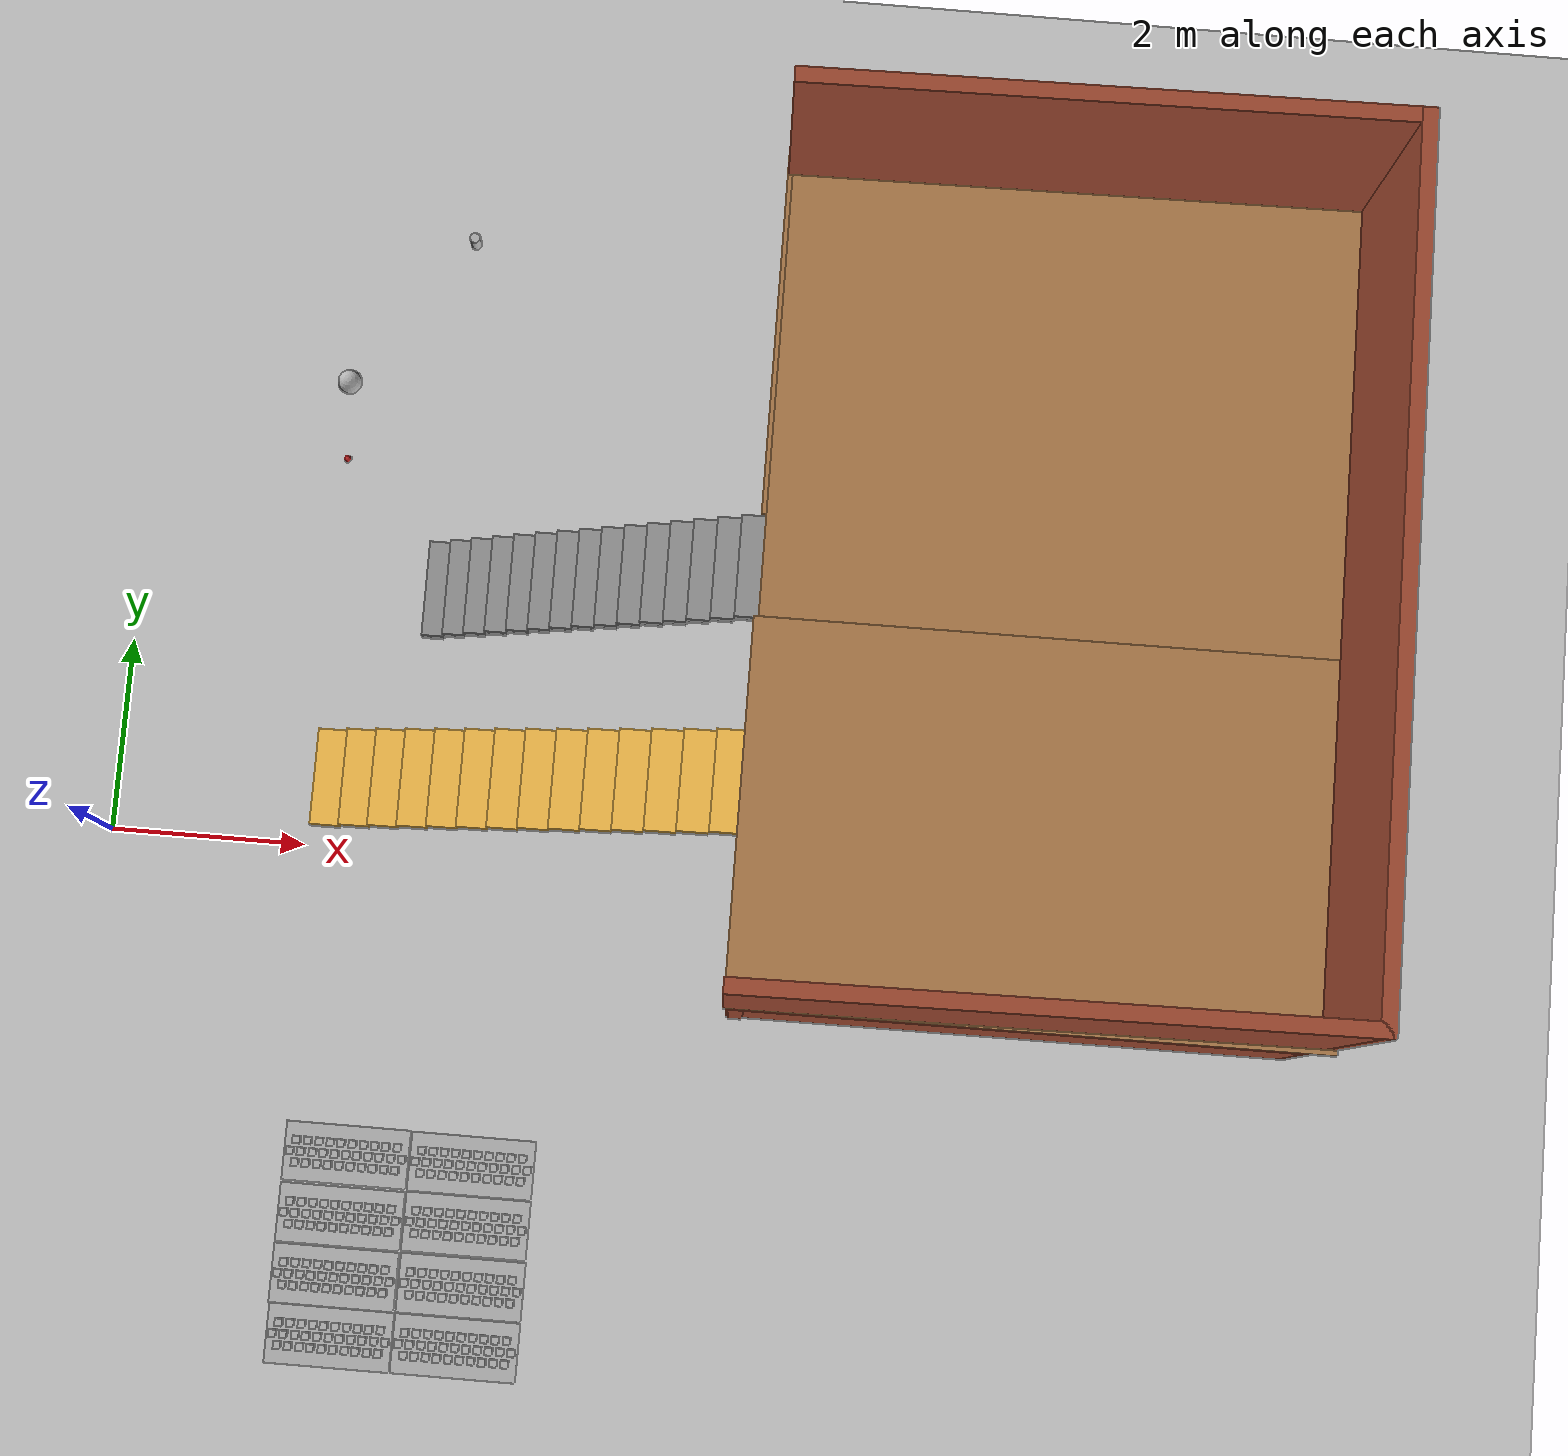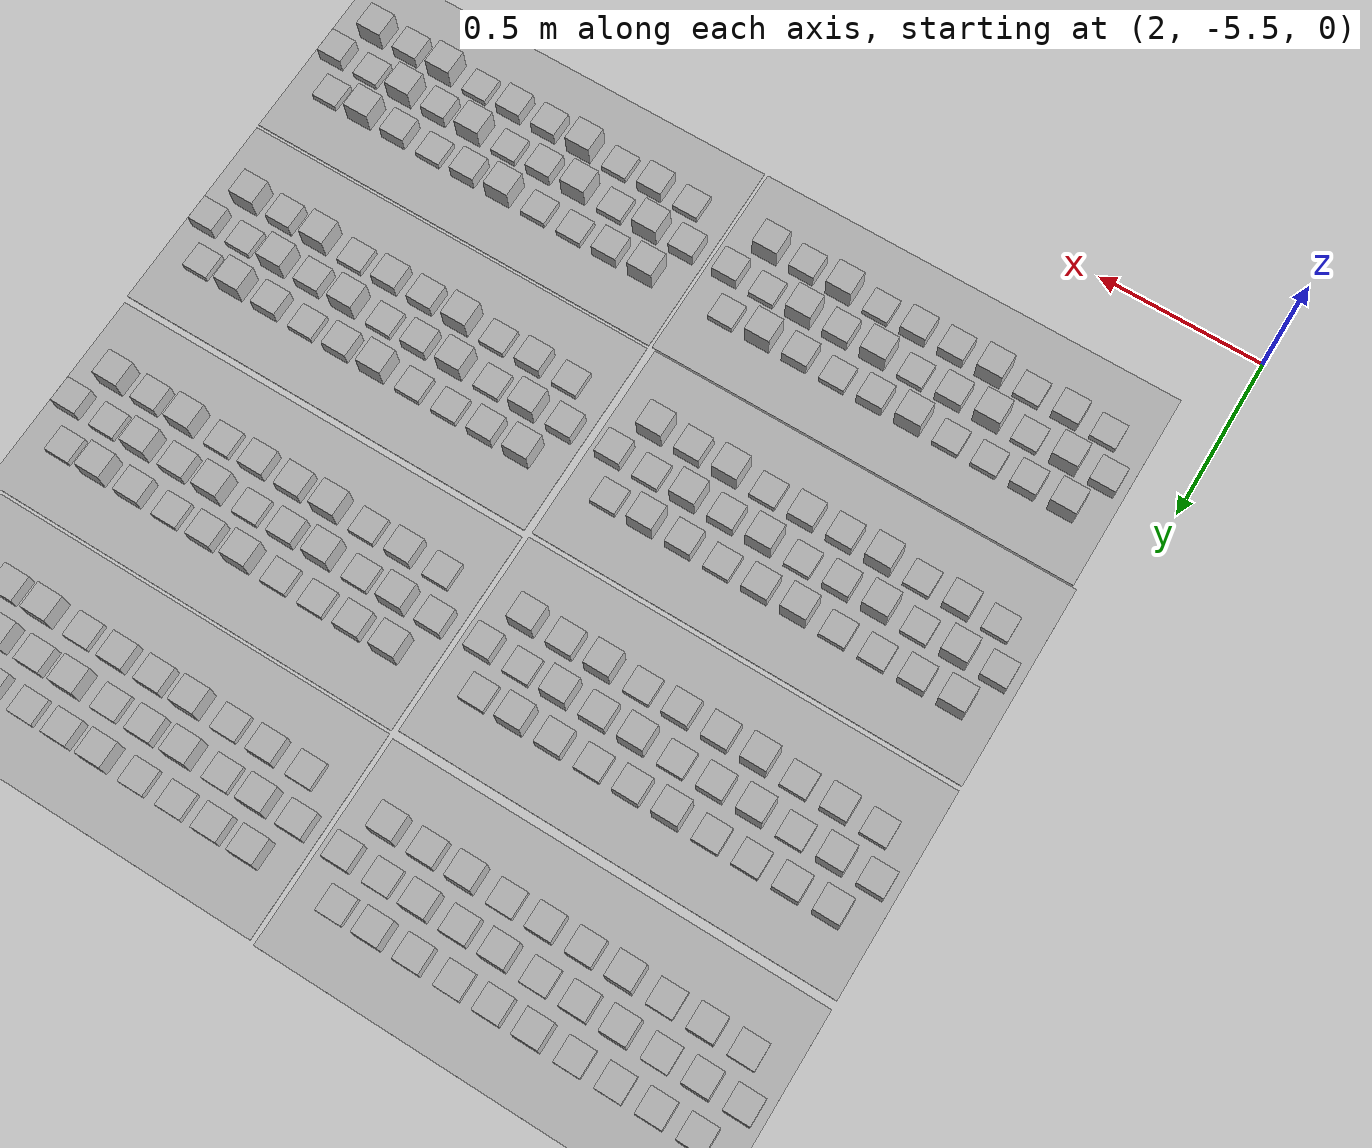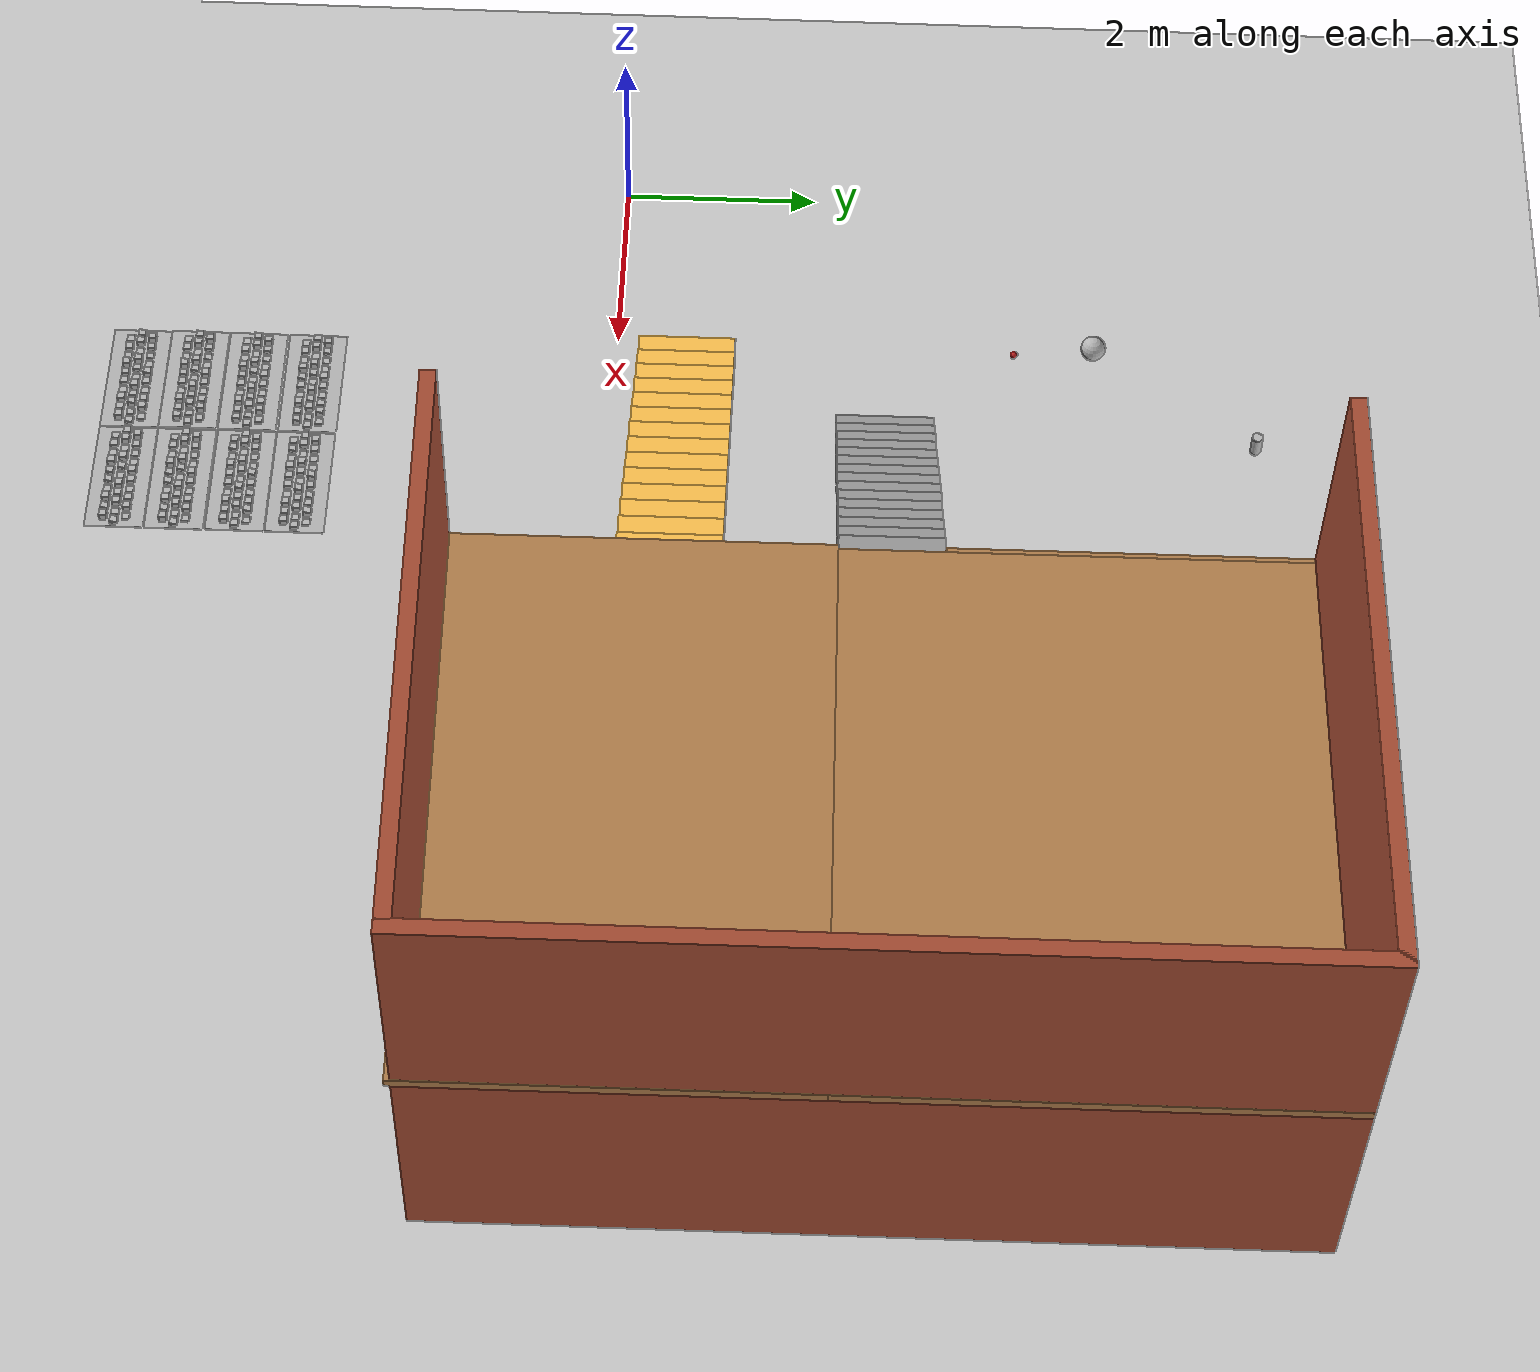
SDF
<sdf version="1.7">
 <world name="default">
  <model name="ground_plane">
   <static>1</static>
   <link name="link">
    <collision name="collision">
     <geometry><plane><normal>0 0 1</normal><size>100 100</size></plane></geometry>
     <surface><friction><ode><mu>100</mu><mu2>50</mu2></ode></friction></surface>
    </collision>
    <visual name="visual">
     <cast_shadows>0</cast_shadows>
     <geometry><plane><normal>0 0 1</normal><size>100 100</size></plane></geometry>
     <material>
      <script><uri>file://media/materials/scripts/gazebo.material</uri><name>Gazebo/Grey</name></script>
     </material>
    </visual>
   </link>
  </model>
  <light name="sun" type="directional">
   <pose>0 0 10 0 -0 0</pose>
   <diffuse>0.8 0.8 0.8 1</diffuse>
   <specular>0.2 0.2 0.2 1</specular>
   <attenuation>
    <range>1000</range>
    <constant>0.9</constant>
    <linear>0.01</linear>
    <quadratic>0.001</quadratic>
   </attenuation>
   <direction>-0.5 0.1 -0.9</direction>
   <spot><inner_angle>0</inner_angle><outer_angle>0</outer_angle><falloff>0</falloff></spot>
  </light>
  <gravity>0 0 -9.8</gravity>
  <magnetic_field>6e-06 2.3e-05 -4.2e-05</magnetic_field>
  <atmosphere type="adiabatic"/>
  <physics type="ode">
   <max_step_size>0.001</max_step_size>
   <real_time_factor>1</real_time_factor>
   <real_time_update_rate>1000</real_time_update_rate>
  </physics>
  <scene><ambient>0.4 0.4 0.4 1</ambient><background>0.7 0.7 0.7 1</background><shadows>1</shadows></scene>
  <spherical_coordinates>
   <surface_model>EARTH_WGS84</surface_model>
   <latitude_deg>0</latitude_deg>
   <longitude_deg>0</longitude_deg>
   <elevation>0</elevation>
   <heading_deg>0</heading_deg>
  </spherical_coordinates>
  <model name="frc2016_ball">
   <pose>1.98556 4.93259 0.127 0 -0 0</pose>
   <link name="link">
    <inertial>
     <mass>0.213</mass>
     <inertia>
      <ixx>0.00322667</ixx>
      <ixy>0</ixy>
      <ixz>0</ixz>
      <iyy>0.00322667</iyy>
      <iyz>0</iyz>
      <izz>0.00322667</izz>
     </inertia>
    </inertial>
    <visual name="visual"><geometry><sphere><radius>0.127</radius></sphere></geometry></visual>
    <collision name="collision">
     <geometry><sphere><radius>0.127</radius></sphere></geometry>
     <surface>
      <bounce><restitution_coefficient>0.15937</restitution_coefficient><threshold>0</threshold></bounce>
      <contact><ode><max_vel>100</max_vel><min_depth>0.001</min_depth></ode></contact>
     </surface>
    </collision>
   </link>
  </model>
  <model name="beer">
   <link name="link">
    <pose>0 0 0.115 0 -0 0</pose>
    <inertial>
     <mass>0.39</mass>
     <inertia><ixx>0.00058</ixx><ixy>0</ixy><ixz>0</ixz><iyy>0.00058</iyy><iyz>0</iyz><izz>0.00019</izz></inertia>
    </inertial>
    <collision name="collision">
     <geometry><cylinder><radius>0.055</radius><length>0.23</length></cylinder></geometry>
    </collision>
    <visual name="visual">
     <geometry><cylinder><radius>0.055</radius><length>0.23</length></cylinder></geometry>
     <material>
      <script>
       <uri>model://beer/materials/scripts</uri>
       <uri>model://beer/materials/textures</uri>
       <name>Beer/Diffuse</name>
      </script>
     </material>
    </visual>
   </link>
   <pose>3.1628 6.57992 -7e-06 0 0 -3.1e-05</pose>
  </model>
  <model name="cricket_ball">
   <link name="link">
    <pose>0 0 0.0375 0 -0 0</pose>
    <inertial>
     <mass>0.1467</mass>
     <inertia>
      <ixx>8.25187e-05</ixx>
      <ixy>0</ixy>
      <ixz>0</ixz>
      <iyy>8.25187e-05</iyy>
      <iyz>0</iyz>
      <izz>8.25187e-05</izz>
     </inertia>
    </inertial>
    <collision name="collision">
     <geometry><sphere><radius>0.0375</radius></sphere></geometry>
     <surface>
      <contact>
       <poissons_ratio>0.347</poissons_ratio>
       <elastic_modulus>8.8e+09</elastic_modulus>
       <ode><kp>100000</kp><kd>100</kd><max_vel>100</max_vel><min_depth>0.001</min_depth></ode>
      </contact>
      <friction>
       <torsional>
        <coefficient>1</coefficient>
        <use_patch_radius>0</use_patch_radius>
        <surface_radius>0.01</surface_radius>
       </torsional>
      </friction>
     </surface>
    </collision>
    <visual name="visual">
     <geometry><sphere><radius>0.0375</radius></sphere></geometry>
     <material>
      <script><uri>file://media/materials/scripts/gazebo.material</uri><name>Gazebo/Red</name></script>
     </material>
    </visual>
    <velocity_decay><linear>0</linear><angular>0.005</angular></velocity_decay>
   </link>
   <pose>2.0353 4.1192 -0.001014 0 -0 0</pose>
  </model>
  <model name="stairs2_0">
   <pose>7.61055 2.7524 0 0 -0 1.5768</pose>
   <link name="Floor_4">
    <pose>-0.01758 -1.72707 2.5 0 -0 0</pose>
    <visual name="Floor_4_Visual_0">
     <pose>-2.30149 0 0.05 0 -0 0</pose>
     <geometry><box><size>3.75682 5.7631 0.1</size></box></geometry>
     <material>
      <script><uri>file://media/materials/scripts/gazebo.material</uri><name>Gazebo/Wood</name></script>
      <ambient>1 1 1 1</ambient>
     </material>
     <meta><layer>1</layer></meta>
    </visual>
    <collision name="Floor_4_Collision_0">
     <geometry><box><size>3.75682 5.7631 0.1</size></box></geometry>
     <pose>-2.30149 0 0.05 0 -0 0</pose>
    </collision>
    <visual name="Floor_4_Visual_1">
     <pose>1.87841 -0.022934 0.05 0 -0 0</pose>
     <geometry><box><size>4.60298 5.71723 0.1</size></box></geometry>
     <material>
      <script><uri>file://media/materials/scripts/gazebo.material</uri><name>Gazebo/Wood</name></script>
      <ambient>1 1 1 1</ambient>
     </material>
     <meta><layer>1</layer></meta>
    </visual>
    <collision name="Floor_4_Collision_1">
     <geometry><box><size>4.60298 5.71723 0.1</size></box></geometry>
     <pose>1.87841 -0.022934 0.05 0 -0 0</pose>
    </collision>
    <visual name="Floor_4_Visual_2">
     <pose>2.37841 2.85862 0.05 0 -0 0</pose>
     <geometry><box><size>3.60298 0.045868 0.1</size></box></geometry>
     <material>
      <script><uri>file://media/materials/scripts/gazebo.material</uri><name>Gazebo/Wood</name></script>
      <ambient>1 1 1 1</ambient>
     </material>
     <meta><layer>1</layer></meta>
    </visual>
    <collision name="Floor_4_Collision_2">
     <geometry><box><size>3.60298 0.045868 0.1</size></box></geometry>
     <pose>2.37841 2.85862 0.05 0 -0 0</pose>
    </collision>
   </link>
   <link name="Stairs_3">
    <visual name="Stairs_3_Visual_0">
     <pose>0.059339 4.49195 0.083333 0 -0 0</pose>
     <geometry><box><size>1 0.233333 0.166667</size></box></geometry>
     <material>
      <script><uri>file://media/materials/scripts/gazebo.material</uri><name>Gazebo/Grey</name></script>
      <ambient>1 1 1 1</ambient>
     </material>
     <meta><layer>0</layer></meta>
    </visual>
    <collision name="Stairs_3_Collision_0">
     <geometry><box><size>1 0.233333 0.166667</size></box></geometry>
     <pose>0.059339 4.49195 0.083333 0 -0 0</pose>
    </collision>
    <visual name="Stairs_3_Visual_1">
     <pose>0.059339 4.25862 0.25 0 -0 0</pose>
     <geometry><box><size>1 0.233333 0.166667</size></box></geometry>
     <material>
      <script><uri>file://media/materials/scripts/gazebo.material</uri><name>Gazebo/Grey</name></script>
      <ambient>1 1 1 1</ambient>
     </material>
     <meta><layer>0</layer></meta>
    </visual>
    <collision name="Stairs_3_Collision_1">
     <geometry><box><size>1 0.233333 0.166667</size></box></geometry>
     <pose>0.059339 4.25862 0.25 0 -0 0</pose>
    </collision>
    <visual name="Stairs_3_Visual_2">
     <pose>0.059339 4.02528 0.416667 0 -0 0</pose>
     <geometry><box><size>1 0.233333 0.166667</size></box></geometry>
     <material>
      <script><uri>file://media/materials/scripts/gazebo.material</uri><name>Gazebo/Grey</name></script>
      <ambient>1 1 1 1</ambient>
     </material>
     <meta><layer>0</layer></meta>
    </visual>
    <collision name="Stairs_3_Collision_2">
     <geometry><box><size>1 0.233333 0.166667</size></box></geometry>
     <pose>0.059339 4.02528 0.416667 0 -0 0</pose>
    </collision>
    <visual name="Stairs_3_Visual_3">
     <pose>0.059339 3.79195 0.583333 0 -0 0</pose>
     <geometry><box><size>1 0.233333 0.166667</size></box></geometry>
     <material>
      <script><uri>file://media/materials/scripts/gazebo.material</uri><name>Gazebo/Grey</name></script>
      <ambient>1 1 1 1</ambient>
     </material>
     <meta><layer>0</layer></meta>
    </visual>
    <collision name="Stairs_3_Collision_3">
     <geometry><box><size>1 0.233333 0.166667</size></box></geometry>
     <pose>0.059339 3.79195 0.583333 0 -0 0</pose>
    </collision>
    <visual name="Stairs_3_Visual_4">
     <pose>0.059339 3.55862 0.75 0 -0 0</pose>
     <geometry><box><size>1 0.233333 0.166667</size></box></geometry>
     <material>
      <script><uri>file://media/materials/scripts/gazebo.material</uri><name>Gazebo/Grey</name></script>
      <ambient>1 1 1 1</ambient>
     </material>
     <meta><layer>0</layer></meta>
    </visual>
    <collision name="Stairs_3_Collision_4">
     <geometry><box><size>1 0.233333 0.166667</size></box></geometry>
     <pose>0.059339 3.55862 0.75 0 -0 0</pose>
    </collision>
    <visual name="Stairs_3_Visual_5">
     <pose>0.059339 3.32528 0.916667 0 -0 0</pose>
     <geometry><box><size>1 0.233333 0.166667</size></box></geometry>
     <material>
      <script><uri>file://media/materials/scripts/gazebo.material</uri><name>Gazebo/Grey</name></script>
      <ambient>1 1 1 1</ambient>
     </material>
     <meta><layer>0</layer></meta>
    </visual>
    <collision name="Stairs_3_Collision_5">
     <geometry><box><size>1 0.233333 0.166667</size></box></geometry>
     <pose>0.059339 3.32528 0.916667 0 -0 0</pose>
    </collision>
    <visual name="Stairs_3_Visual_6">
     <pose>0.059339 3.09195 1.08333 0 -0 0</pose>
     <geometry><box><size>1 0.233333 0.166667</size></box></geometry>
     <material>
      <script><uri>file://media/materials/scripts/gazebo.material</uri><name>Gazebo/Grey</name></script>
      <ambient>1 1 1 1</ambient>
     </material>
     <meta><layer>0</layer></meta>
    </visual>
    <collision name="Stairs_3_Collision_6">
     <geometry><box><size>1 0.233333 0.166667</size></box></geometry>
     <pose>0.059339 3.09195 1.08333 0 -0 0</pose>
    </collision>
    <visual name="Stairs_3_Visual_7">
     <pose>0.059339 2.85862 1.25 0 -0 0</pose>
     <geometry><box><size>1 0.233333 0.166667</size></box></geometry>
     <material>
      <script><uri>file://media/materials/scripts/gazebo.material</uri><name>Gazebo/Grey</name></script>
      <ambient>1 1 1 1</ambient>
     </material>
     <meta><layer>0</layer></meta>
    </visual>
    <collision name="Stairs_3_Collision_7">
     <geometry><box><size>1 0.233333 0.166667</size></box></geometry>
     <pose>0.059339 2.85862 1.25 0 -0 0</pose>
    </collision>
    <visual name="Stairs_3_Visual_8">
     <pose>0.059339 2.62528 1.41667 0 -0 0</pose>
     <geometry><box><size>1 0.233333 0.166667</size></box></geometry>
     <material>
      <script><uri>file://media/materials/scripts/gazebo.material</uri><name>Gazebo/Grey</name></script>
      <ambient>1 1 1 1</ambient>
     </material>
     <meta><layer>0</layer></meta>
    </visual>
    <collision name="Stairs_3_Collision_8">
     <geometry><box><size>1 0.233333 0.166667</size></box></geometry>
     <pose>0.059339 2.62528 1.41667 0 -0 0</pose>
    </collision>
    <visual name="Stairs_3_Visual_9">
     <pose>0.059339 2.39195 1.58333 0 -0 0</pose>
     <geometry><box><size>1 0.233333 0.166667</size></box></geometry>
     <material>
      <script><uri>file://media/materials/scripts/gazebo.material</uri><name>Gazebo/Grey</name></script>
      <ambient>1 1 1 1</ambient>
     </material>
     <meta><layer>0</layer></meta>
    </visual>
    <collision name="Stairs_3_Collision_9">
     <geometry><box><size>1 0.233333 0.166667</size></box></geometry>
     <pose>0.059339 2.39195 1.58333 0 -0 0</pose>
    </collision>
    <visual name="Stairs_3_Visual_10">
     <pose>0.059339 2.15862 1.75 0 -0 0</pose>
     <geometry><box><size>1 0.233333 0.166667</size></box></geometry>
     <material>
      <script><uri>file://media/materials/scripts/gazebo.material</uri><name>Gazebo/Grey</name></script>
      <ambient>1 1 1 1</ambient>
     </material>
     <meta><layer>0</layer></meta>
    </visual>
    <collision name="Stairs_3_Collision_10">
     <geometry><box><size>1 0.233333 0.166667</size></box></geometry>
     <pose>0.059339 2.15862 1.75 0 -0 0</pose>
    </collision>
    <visual name="Stairs_3_Visual_11">
     <pose>0.059339 1.92528 1.91667 0 -0 0</pose>
     <geometry><box><size>1 0.233333 0.166667</size></box></geometry>
     <material>
      <script><uri>file://media/materials/scripts/gazebo.material</uri><name>Gazebo/Grey</name></script>
      <ambient>1 1 1 1</ambient>
     </material>
     <meta><layer>0</layer></meta>
    </visual>
    <collision name="Stairs_3_Collision_11">
     <geometry><box><size>1 0.233333 0.166667</size></box></geometry>
     <pose>0.059339 1.92528 1.91667 0 -0 0</pose>
    </collision>
    <visual name="Stairs_3_Visual_12">
     <pose>0.059339 1.69195 2.08333 0 -0 0</pose>
     <geometry><box><size>1 0.233333 0.166667</size></box></geometry>
     <material>
      <script><uri>file://media/materials/scripts/gazebo.material</uri><name>Gazebo/Grey</name></script>
      <ambient>1 1 1 1</ambient>
     </material>
     <meta><layer>0</layer></meta>
    </visual>
    <collision name="Stairs_3_Collision_12">
     <geometry><box><size>1 0.233333 0.166667</size></box></geometry>
     <pose>0.059339 1.69195 2.08333 0 -0 0</pose>
    </collision>
    <visual name="Stairs_3_Visual_13">
     <pose>0.059339 1.45862 2.25 0 -0 0</pose>
     <geometry><box><size>1 0.233333 0.166667</size></box></geometry>
     <material>
      <script><uri>file://media/materials/scripts/gazebo.material</uri><name>Gazebo/Grey</name></script>
      <ambient>1 1 1 1</ambient>
     </material>
     <meta><layer>0</layer></meta>
    </visual>
    <collision name="Stairs_3_Collision_13">
     <geometry><box><size>1 0.233333 0.166667</size></box></geometry>
     <pose>0.059339 1.45862 2.25 0 -0 0</pose>
    </collision>
    <visual name="Stairs_3_Visual_14">
     <pose>0.059339 1.22528 2.41667 0 -0 0</pose>
     <geometry><box><size>1 0.233333 0.166667</size></box></geometry>
     <material>
      <script><uri>file://media/materials/scripts/gazebo.material</uri><name>Gazebo/Grey</name></script>
      <ambient>1 1 1 1</ambient>
     </material>
     <meta><layer>0</layer></meta>
    </visual>
    <collision name="Stairs_3_Collision_14">
     <geometry><box><size>1 0.233333 0.166667</size></box></geometry>
     <pose>0.059339 1.22528 2.41667 0 -0 0</pose>
    </collision>
   </link>
   <link name="Wall_44">
    <collision name="Wall_44_Collision">
     <geometry><box><size>5.70366 0.15 2.5</size></box></geometry>
     <pose>0 0 1.25 0 -0 0</pose>
    </collision>
    <visual name="Wall_44_Visual">
     <pose>0 0 1.25 0 -0 0</pose>
     <geometry><box><size>5.70366 0.15 2.5</size></box></geometry>
     <material>
      <script><uri>file://media/materials/scripts/gazebo.material</uri><name>Gazebo/Bricks</name></script>
      <ambient>1 1 1 1</ambient>
     </material>
     <meta><layer>0</layer></meta>
    </visual>
    <pose>-4.0693 -1.71554 0 0 -0 -1.5708</pose>
   </link>
   <link name="Wall_45">
    <collision name="Wall_45_Collision">
     <geometry><box><size>8.30592 0.15 2.5</size></box></geometry>
     <pose>0 0 1.25 0 -0 0</pose>
    </collision>
    <visual name="Wall_45_Visual">
     <pose>0 0 1.25 0 -0 0</pose>
     <geometry><box><size>8.30592 0.15 2.5</size></box></geometry>
     <material>
      <script><uri>file://media/materials/scripts/gazebo.material</uri><name>Gazebo/Bricks</name></script>
      <ambient>1 1 1 1</ambient>
     </material>
     <meta><layer>0</layer></meta>
    </visual>
    <pose>0.008655 -4.53046 0 0 -0 -0.000761</pose>
   </link>
   <link name="Wall_46">
    <collision name="Wall_46_Collision">
     <geometry><box><size>5.6862 0.15 2.5</size></box></geometry>
     <pose>0 0 1.25 0 -0 0</pose>
    </collision>
    <visual name="Wall_46_Visual">
     <pose>0 0 1.25 0 -0 0</pose>
     <geometry><box><size>5.6862 0.15 2.5</size></box></geometry>
     <material>
      <script><uri>file://media/materials/scripts/gazebo.material</uri><name>Gazebo/Bricks</name></script>
      <ambient>1 1 1 1</ambient>
     </material>
     <meta><layer>0</layer></meta>
    </visual>
    <pose>4.07787 -1.73049 0 0 -0 1.57396</pose>
   </link>
   <link name="Wall_47">
    <collision name="Wall_47_Collision">
     <geometry><box><size>8.30592 0.15 2.5</size></box></geometry>
     <pose>0 0 1.25 0 -0 0</pose>
    </collision>
    <visual name="Wall_47_Visual">
     <pose>0 0 1.25 0 -0 0</pose>
     <geometry><box><size>8.30592 0.15 2.5</size></box></geometry>
     <material>
      <script><uri>file://media/materials/scripts/gazebo.material</uri><name>Gazebo/Bricks</name></script>
      <ambient>1 1 1 1</ambient>
     </material>
     <meta><layer>0</layer></meta>
    </visual>
    <pose>-0.008835 1.0407 0 0 -0 3.14083</pose>
   </link>
   <link name="Wall_49">
    <collision name="Wall_49_Collision">
     <geometry><box><size>5.7214 0.15 2.5</size></box></geometry>
     <pose>0 0 1.25 0 -0 0</pose>
    </collision>
    <visual name="Wall_49_Visual">
     <pose>0 0 1.25 0 -0 0</pose>
     <geometry><box><size>5.7214 0.15 2.5</size></box></geometry>
     <material>
      <script><uri>file://media/materials/scripts/gazebo.material</uri><name>Gazebo/Bricks</name></script>
      <ambient>1 1 1 1</ambient>
     </material>
     <meta><layer>1</layer></meta>
    </visual>
    <pose>-4.09554 -1.7068 2.5 0 -0 -1.56138</pose>
   </link>
   <link name="Wall_50">
    <collision name="Wall_50_Collision">
     <geometry><box><size>8.30592 0.15 2.5</size></box></geometry>
     <pose>0 0 1.25 0 -0 0</pose>
    </collision>
    <visual name="Wall_50_Visual">
     <pose>0 0 1.25 0 -0 0</pose>
     <geometry><box><size>8.30592 0.15 2.5</size></box></geometry>
     <material>
      <script><uri>file://media/materials/scripts/gazebo.material</uri><name>Gazebo/Bricks</name></script>
      <ambient>1 1 1 1</ambient>
     </material>
     <meta><layer>1</layer></meta>
    </visual>
    <pose>0.008655 -4.53045 2.5 0 -0 -0.000761</pose>
   </link>
   <link name="Wall_51">
    <collision name="Wall_51_Collision">
     <geometry><box><size>5.7214 0.15 2.5</size></box></geometry>
     <pose>0 0 1.25 0 -0 0</pose>
    </collision>
    <visual name="Wall_51_Visual">
     <pose>0 0 1.25 0 -0 0</pose>
     <geometry><box><size>5.7214 0.15 2.5</size></box></geometry>
     <material>
      <script><uri>file://media/materials/scripts/gazebo.material</uri><name>Gazebo/Bricks</name></script>
      <ambient>1 1 1 1</ambient>
     </material>
     <meta><layer>1</layer></meta>
    </visual>
    <pose>4.06038 -1.713 2.5 0 -0 1.58021</pose>
   </link>
   <static>1</static>
  </model>
  <model name="frc2016_roughterrain">
   <static>1</static>
   <link name="link">
    <visual name="platform">
     <pose>0 0 0.08269 0 -0 0</pose>
     <geometry><box><size>1.27 0.5969 0.003175</size></box></geometry>
    </visual>
    <collision name="platform">
     <pose>0 0 0.08269 0 -0 0</pose>
     <geometry><box><size>1.27 0.5969 0.003175</size></box></geometry>
    </collision>
    <visual name="row1_block1_sm">
     <pose>0.51435 0.1143 0.09698 0 -0 0</pose>
     <geometry><box><size>0.0762 0.0762 0.0254</size></box></geometry>
    </visual>
    <collision name="row1_block1_sm">
     <pose>0.51435 0.1143 0.09698 0 -0 0</pose>
     <geometry><box><size>0.0762 0.0762 0.0254</size></box></geometry>
    </collision>
    <visual name="row1_block2_lg">
     <pose>0.40005 0.1143 0.12238 0 -0 0</pose>
     <geometry><box><size>0.0762 0.0762 0.0762</size></box></geometry>
    </visual>
    <collision name="row1_block2_lg">
     <pose>0.40005 0.1143 0.12238 0 -0 0</pose>
     <geometry><box><size>0.0762 0.0762 0.0762</size></box></geometry>
    </collision>
    <visual name="row1_block3_md">
     <pose>0.28575 0.1143 0.10968 0 -0 0</pose>
     <geometry><box><size>0.0762 0.0762 0.0508</size></box></geometry>
    </visual>
    <collision name="row1_block3_md">
     <pose>0.28575 0.1143 0.10968 0 -0 0</pose>
     <geometry><box><size>0.0762 0.0762 0.0508</size></box></geometry>
    </collision>
    <visual name="row1_block4_sm">
     <pose>0.17145 0.1143 0.09698 0 -0 0</pose>
     <geometry><box><size>0.0762 0.0762 0.0254</size></box></geometry>
    </visual>
    <collision name="row1_block4_sm">
     <pose>0.17145 0.1143 0.09698 0 -0 0</pose>
     <geometry><box><size>0.0762 0.0762 0.0254</size></box></geometry>
    </collision>
    <visual name="row1_block5_md">
     <pose>0.05715 0.1143 0.10968 0 -0 0</pose>
     <geometry><box><size>0.0762 0.0762 0.0508</size></box></geometry>
    </visual>
    <collision name="row1_block5_md">
     <pose>0.05715 0.1143 0.10968 0 -0 0</pose>
     <geometry><box><size>0.0762 0.0762 0.0508</size></box></geometry>
    </collision>
    <visual name="row1_block6_lg">
     <pose>-0.05715 0.1143 0.12238 0 -0 0</pose>
     <geometry><box><size>0.0762 0.0762 0.0762</size></box></geometry>
    </visual>
    <collision name="row1_block6_lg">
     <pose>-0.05715 0.1143 0.12238 0 -0 0</pose>
     <geometry><box><size>0.0762 0.0762 0.0762</size></box></geometry>
    </collision>
    <visual name="row1_block7_sm">
     <pose>-0.17145 0.1143 0.09698 0 -0 0</pose>
     <geometry><box><size>0.0762 0.0762 0.0254</size></box></geometry>
    </visual>
    <collision name="row1_block7_sm">
     <pose>-0.17145 0.1143 0.09698 0 -0 0</pose>
     <geometry><box><size>0.0762 0.0762 0.0254</size></box></geometry>
    </collision>
    <visual name="row1_block8_sm">
     <pose>-0.28575 0.1143 0.09698 0 -0 0</pose>
     <geometry><box><size>0.0762 0.0762 0.0254</size></box></geometry>
    </visual>
    <collision name="row1_block8_sm">
     <pose>-0.28575 0.1143 0.09698 0 -0 0</pose>
     <geometry><box><size>0.0762 0.0762 0.0254</size></box></geometry>
    </collision>
    <visual name="row1_block9_md">
     <pose>-0.40005 0.1143 0.10968 0 -0 0</pose>
     <geometry><box><size>0.0762 0.0762 0.0508</size></box></geometry>
    </visual>
    <collision name="row1_block9_md">
     <pose>-0.40005 0.1143 0.10968 0 -0 0</pose>
     <geometry><box><size>0.0762 0.0762 0.0508</size></box></geometry>
    </collision>
    <visual name="row1_block10_lg">
     <pose>-0.51435 0.1143 0.12238 0 -0 0</pose>
     <geometry><box><size>0.0762 0.0762 0.0762</size></box></geometry>
    </visual>
    <collision name="row1_block10_lg">
     <pose>-0.51435 0.1143 0.12238 0 -0 0</pose>
     <geometry><box><size>0.0762 0.0762 0.0762</size></box></geometry>
    </collision>
    <visual name="row2_block1_md">
     <pose>0.5715 0 0.10968 0 -0 0</pose>
     <geometry><box><size>0.0762 0.0762 0.0508</size></box></geometry>
    </visual>
    <collision name="row2_block1_md">
     <pose>0.5715 0 0.10968 0 -0 0</pose>
     <geometry><box><size>0.0762 0.0762 0.0508</size></box></geometry>
    </collision>
    <visual name="row2_block2_sm">
     <pose>0.4572 0 0.09698 0 -0 0</pose>
     <geometry><box><size>0.0762 0.0762 0.0254</size></box></geometry>
    </visual>
    <collision name="row2_block2_sm">
     <pose>0.4572 0 0.09698 0 -0 0</pose>
     <geometry><box><size>0.0762 0.0762 0.0254</size></box></geometry>
    </collision>
    <visual name="row2_block3_lg">
     <pose>0.3429 0 0.12238 0 -0 0</pose>
     <geometry><box><size>0.0762 0.0762 0.0762</size></box></geometry>
    </visual>
    <collision name="row2_block3_lg">
     <pose>0.3429 0 0.12238 0 -0 0</pose>
     <geometry><box><size>0.0762 0.0762 0.0762</size></box></geometry>
    </collision>
    <visual name="row2_block4_md">
     <pose>0.2286 0 0.10968 0 -0 0</pose>
     <geometry><box><size>0.0762 0.0762 0.0508</size></box></geometry>
    </visual>
    <collision name="row2_block4_md">
     <pose>0.2286 0 0.10968 0 -0 0</pose>
     <geometry><box><size>0.0762 0.0762 0.0508</size></box></geometry>
    </collision>
    <visual name="row2_block5_lg">
     <pose>0.1143 0 0.12238 0 -0 0</pose>
     <geometry><box><size>0.0762 0.0762 0.0762</size></box></geometry>
    </visual>
    <collision name="row2_block5_lg">
     <pose>0.1143 0 0.12238 0 -0 0</pose>
     <geometry><box><size>0.0762 0.0762 0.0762</size></box></geometry>
    </collision>
    <visual name="row2_block6_sm">
     <pose>0 0 0.09698 0 -0 0</pose>
     <geometry><box><size>0.0762 0.0762 0.0254</size></box></geometry>
    </visual>
    <collision name="row2_block6_sm">
     <pose>0 0 0.09698 0 -0 0</pose>
     <geometry><box><size>0.0762 0.0762 0.0254</size></box></geometry>
    </collision>
    <visual name="row2_block7_md">
     <pose>-0.1143 0 0.10968 0 -0 0</pose>
     <geometry><box><size>0.0762 0.0762 0.0508</size></box></geometry>
    </visual>
    <collision name="row2_block7_md">
     <pose>-0.1143 0 0.10968 0 -0 0</pose>
     <geometry><box><size>0.0762 0.0762 0.0508</size></box></geometry>
    </collision>
    <visual name="row2_block8_lg">
     <pose>-0.2286 0 0.12238 0 -0 0</pose>
     <geometry><box><size>0.0762 0.0762 0.0762</size></box></geometry>
    </visual>
    <collision name="row2_block8_lg">
     <pose>-0.2286 0 0.12238 0 -0 0</pose>
     <geometry><box><size>0.0762 0.0762 0.0762</size></box></geometry>
    </collision>
    <visual name="row2_block9_sm">
     <pose>-0.3429 0 0.09698 0 -0 0</pose>
     <geometry><box><size>0.0762 0.0762 0.0254</size></box></geometry>
    </visual>
    <collision name="row2_block9_sm">
     <pose>-0.3429 0 0.09698 0 -0 0</pose>
     <geometry><box><size>0.0762 0.0762 0.0254</size></box></geometry>
    </collision>
    <visual name="row2_block10_lg">
     <pose>-0.4572 0 0.12238 0 -0 0</pose>
     <geometry><box><size>0.0762 0.0762 0.0762</size></box></geometry>
    </visual>
    <collision name="row2_block10_lg">
     <pose>-0.4572 0 0.12238 0 -0 0</pose>
     <geometry><box><size>0.0762 0.0762 0.0762</size></box></geometry>
    </collision>
    <visual name="row2_block11_md">
     <pose>-0.5715 0 0.10968 0 -0 0</pose>
     <geometry><box><size>0.0762 0.0762 0.0508</size></box></geometry>
    </visual>
    <collision name="row2_block11_md">
     <pose>-0.5715 0 0.10968 0 -0 0</pose>
     <geometry><box><size>0.0762 0.0762 0.0508</size></box></geometry>
    </collision>
    <visual name="row3_block1_lg">
     <pose>0.51435 -0.1143 0.12238 0 -0 0</pose>
     <geometry><box><size>0.0762 0.0762 0.0762</size></box></geometry>
    </visual>
    <collision name="row3_block1_lg">
     <pose>0.51435 -0.1143 0.12238 0 -0 0</pose>
     <geometry><box><size>0.0762 0.0762 0.0762</size></box></geometry>
    </collision>
    <visual name="row3_block2_md">
     <pose>0.40005 -0.1143 0.10968 0 -0 0</pose>
     <geometry><box><size>0.0762 0.0762 0.0508</size></box></geometry>
    </visual>
    <collision name="row3_block2_md">
     <pose>0.40005 -0.1143 0.10968 0 -0 0</pose>
     <geometry><box><size>0.0762 0.0762 0.0508</size></box></geometry>
    </collision>
    <visual name="row3_block3_lg">
     <pose>0.28575 -0.1143 0.12238 0 -0 0</pose>
     <geometry><box><size>0.0762 0.0762 0.0762</size></box></geometry>
    </visual>
    <collision name="row3_block3_lg">
     <pose>0.28575 -0.1143 0.12238 0 -0 0</pose>
     <geometry><box><size>0.0762 0.0762 0.0762</size></box></geometry>
    </collision>
    <visual name="row3_block4_sm">
     <pose>0.17145 -0.1143 0.09698 0 -0 0</pose>
     <geometry><box><size>0.0762 0.0762 0.0254</size></box></geometry>
    </visual>
    <collision name="row3_block4_sm">
     <pose>0.17145 -0.1143 0.09698 0 -0 0</pose>
     <geometry><box><size>0.0762 0.0762 0.0254</size></box></geometry>
    </collision>
    <visual name="row3_block5_md">
     <pose>0.05715 -0.1143 0.10968 0 -0 0</pose>
     <geometry><box><size>0.0762 0.0762 0.0508</size></box></geometry>
    </visual>
    <collision name="row3_block5_md">
     <pose>0.05715 -0.1143 0.10968 0 -0 0</pose>
     <geometry><box><size>0.0762 0.0762 0.0508</size></box></geometry>
    </collision>
    <visual name="row3_block6_md">
     <pose>-0.05715 -0.1143 0.10968 0 -0 0</pose>
     <geometry><box><size>0.0762 0.0762 0.0508</size></box></geometry>
    </visual>
    <collision name="row3_block6_md">
     <pose>-0.05715 -0.1143 0.10968 0 -0 0</pose>
     <geometry><box><size>0.0762 0.0762 0.0508</size></box></geometry>
    </collision>
    <visual name="row3_block7_lg">
     <pose>-0.17145 -0.1143 0.12238 0 -0 0</pose>
     <geometry><box><size>0.0762 0.0762 0.0762</size></box></geometry>
    </visual>
    <collision name="row3_block7_lg">
     <pose>-0.17145 -0.1143 0.12238 0 -0 0</pose>
     <geometry><box><size>0.0762 0.0762 0.0762</size></box></geometry>
    </collision>
    <visual name="row3_block8_sm">
     <pose>-0.28575 -0.1143 0.09698 0 -0 0</pose>
     <geometry><box><size>0.0762 0.0762 0.0254</size></box></geometry>
    </visual>
    <collision name="row3_block8_sm">
     <pose>-0.28575 -0.1143 0.09698 0 -0 0</pose>
     <geometry><box><size>0.0762 0.0762 0.0254</size></box></geometry>
    </collision>
    <visual name="row3_block9_md">
     <pose>-0.40005 -0.1143 0.10968 0 -0 0</pose>
     <geometry><box><size>0.0762 0.0762 0.0508</size></box></geometry>
    </visual>
    <collision name="row3_block9_md">
     <pose>-0.40005 -0.1143 0.10968 0 -0 0</pose>
     <geometry><box><size>0.0762 0.0762 0.0508</size></box></geometry>
    </collision>
    <visual name="row3_block10_sm">
     <pose>-0.51435 -0.1143 0.09698 0 -0 0</pose>
     <geometry><box><size>0.0762 0.0762 0.0254</size></box></geometry>
    </visual>
    <collision name="row3_block10_sm">
     <pose>-0.51435 -0.1143 0.09698 0 -0 0</pose>
     <geometry><box><size>0.0762 0.0762 0.0254</size></box></geometry>
    </collision>
   </link>
   <pose>4.04617 -3.73596 0 0 -0 0</pose>
  </model>
  <model name="frc2016_roughterrain_0">
   <static>1</static>
   <link name="link">
    <visual name="platform">
     <pose>0 0 0.08269 0 -0 0</pose>
     <geometry><box><size>1.27 0.5969 0.003175</size></box></geometry>
    </visual>
    <collision name="platform">
     <pose>0 0 0.08269 0 -0 0</pose>
     <geometry><box><size>1.27 0.5969 0.003175</size></box></geometry>
    </collision>
    <visual name="row1_block1_sm">
     <pose>0.51435 0.1143 0.09698 0 -0 0</pose>
     <geometry><box><size>0.0762 0.0762 0.0254</size></box></geometry>
    </visual>
    <collision name="row1_block1_sm">
     <pose>0.51435 0.1143 0.09698 0 -0 0</pose>
     <geometry><box><size>0.0762 0.0762 0.0254</size></box></geometry>
    </collision>
    <visual name="row1_block2_lg">
     <pose>0.40005 0.1143 0.12238 0 -0 0</pose>
     <geometry><box><size>0.0762 0.0762 0.0762</size></box></geometry>
    </visual>
    <collision name="row1_block2_lg">
     <pose>0.40005 0.1143 0.12238 0 -0 0</pose>
     <geometry><box><size>0.0762 0.0762 0.0762</size></box></geometry>
    </collision>
    <visual name="row1_block3_md">
     <pose>0.28575 0.1143 0.10968 0 -0 0</pose>
     <geometry><box><size>0.0762 0.0762 0.0508</size></box></geometry>
    </visual>
    <collision name="row1_block3_md">
     <pose>0.28575 0.1143 0.10968 0 -0 0</pose>
     <geometry><box><size>0.0762 0.0762 0.0508</size></box></geometry>
    </collision>
    <visual name="row1_block4_sm">
     <pose>0.17145 0.1143 0.09698 0 -0 0</pose>
     <geometry><box><size>0.0762 0.0762 0.0254</size></box></geometry>
    </visual>
    <collision name="row1_block4_sm">
     <pose>0.17145 0.1143 0.09698 0 -0 0</pose>
     <geometry><box><size>0.0762 0.0762 0.0254</size></box></geometry>
    </collision>
    <visual name="row1_block5_md">
     <pose>0.05715 0.1143 0.10968 0 -0 0</pose>
     <geometry><box><size>0.0762 0.0762 0.0508</size></box></geometry>
    </visual>
    <collision name="row1_block5_md">
     <pose>0.05715 0.1143 0.10968 0 -0 0</pose>
     <geometry><box><size>0.0762 0.0762 0.0508</size></box></geometry>
    </collision>
    <visual name="row1_block6_lg">
     <pose>-0.05715 0.1143 0.12238 0 -0 0</pose>
     <geometry><box><size>0.0762 0.0762 0.0762</size></box></geometry>
    </visual>
    <collision name="row1_block6_lg">
     <pose>-0.05715 0.1143 0.12238 0 -0 0</pose>
     <geometry><box><size>0.0762 0.0762 0.0762</size></box></geometry>
    </collision>
    <visual name="row1_block7_sm">
     <pose>-0.17145 0.1143 0.09698 0 -0 0</pose>
     <geometry><box><size>0.0762 0.0762 0.0254</size></box></geometry>
    </visual>
    <collision name="row1_block7_sm">
     <pose>-0.17145 0.1143 0.09698 0 -0 0</pose>
     <geometry><box><size>0.0762 0.0762 0.0254</size></box></geometry>
    </collision>
    <visual name="row1_block8_sm">
     <pose>-0.28575 0.1143 0.09698 0 -0 0</pose>
     <geometry><box><size>0.0762 0.0762 0.0254</size></box></geometry>
    </visual>
    <collision name="row1_block8_sm">
     <pose>-0.28575 0.1143 0.09698 0 -0 0</pose>
     <geometry><box><size>0.0762 0.0762 0.0254</size></box></geometry>
    </collision>
    <visual name="row1_block9_md">
     <pose>-0.40005 0.1143 0.10968 0 -0 0</pose>
     <geometry><box><size>0.0762 0.0762 0.0508</size></box></geometry>
    </visual>
    <collision name="row1_block9_md">
     <pose>-0.40005 0.1143 0.10968 0 -0 0</pose>
     <geometry><box><size>0.0762 0.0762 0.0508</size></box></geometry>
    </collision>
    <visual name="row1_block10_lg">
     <pose>-0.51435 0.1143 0.12238 0 -0 0</pose>
     <geometry><box><size>0.0762 0.0762 0.0762</size></box></geometry>
    </visual>
    <collision name="row1_block10_lg">
     <pose>-0.51435 0.1143 0.12238 0 -0 0</pose>
     <geometry><box><size>0.0762 0.0762 0.0762</size></box></geometry>
    </collision>
    <visual name="row2_block1_md">
     <pose>0.5715 0 0.10968 0 -0 0</pose>
     <geometry><box><size>0.0762 0.0762 0.0508</size></box></geometry>
    </visual>
    <collision name="row2_block1_md">
     <pose>0.5715 0 0.10968 0 -0 0</pose>
     <geometry><box><size>0.0762 0.0762 0.0508</size></box></geometry>
    </collision>
    <visual name="row2_block2_sm">
     <pose>0.4572 0 0.09698 0 -0 0</pose>
     <geometry><box><size>0.0762 0.0762 0.0254</size></box></geometry>
    </visual>
    <collision name="row2_block2_sm">
     <pose>0.4572 0 0.09698 0 -0 0</pose>
     <geometry><box><size>0.0762 0.0762 0.0254</size></box></geometry>
    </collision>
    <visual name="row2_block3_lg">
     <pose>0.3429 0 0.12238 0 -0 0</pose>
     <geometry><box><size>0.0762 0.0762 0.0762</size></box></geometry>
    </visual>
    <collision name="row2_block3_lg">
     <pose>0.3429 0 0.12238 0 -0 0</pose>
     <geometry><box><size>0.0762 0.0762 0.0762</size></box></geometry>
    </collision>
    <visual name="row2_block4_md">
     <pose>0.2286 0 0.10968 0 -0 0</pose>
     <geometry><box><size>0.0762 0.0762 0.0508</size></box></geometry>
    </visual>
    <collision name="row2_block4_md">
     <pose>0.2286 0 0.10968 0 -0 0</pose>
     <geometry><box><size>0.0762 0.0762 0.0508</size></box></geometry>
    </collision>
    <visual name="row2_block5_lg">
     <pose>0.1143 0 0.12238 0 -0 0</pose>
     <geometry><box><size>0.0762 0.0762 0.0762</size></box></geometry>
    </visual>
    <collision name="row2_block5_lg">
     <pose>0.1143 0 0.12238 0 -0 0</pose>
     <geometry><box><size>0.0762 0.0762 0.0762</size></box></geometry>
    </collision>
    <visual name="row2_block6_sm">
     <pose>0 0 0.09698 0 -0 0</pose>
     <geometry><box><size>0.0762 0.0762 0.0254</size></box></geometry>
    </visual>
    <collision name="row2_block6_sm">
     <pose>0 0 0.09698 0 -0 0</pose>
     <geometry><box><size>0.0762 0.0762 0.0254</size></box></geometry>
    </collision>
    <visual name="row2_block7_md">
     <pose>-0.1143 0 0.10968 0 -0 0</pose>
     <geometry><box><size>0.0762 0.0762 0.0508</size></box></geometry>
    </visual>
    <collision name="row2_block7_md">
     <pose>-0.1143 0 0.10968 0 -0 0</pose>
     <geometry><box><size>0.0762 0.0762 0.0508</size></box></geometry>
    </collision>
    <visual name="row2_block8_lg">
     <pose>-0.2286 0 0.12238 0 -0 0</pose>
     <geometry><box><size>0.0762 0.0762 0.0762</size></box></geometry>
    </visual>
    <collision name="row2_block8_lg">
     <pose>-0.2286 0 0.12238 0 -0 0</pose>
     <geometry><box><size>0.0762 0.0762 0.0762</size></box></geometry>
    </collision>
    <visual name="row2_block9_sm">
     <pose>-0.3429 0 0.09698 0 -0 0</pose>
     <geometry><box><size>0.0762 0.0762 0.0254</size></box></geometry>
    </visual>
    <collision name="row2_block9_sm">
     <pose>-0.3429 0 0.09698 0 -0 0</pose>
     <geometry><box><size>0.0762 0.0762 0.0254</size></box></geometry>
    </collision>
    <visual name="row2_block10_lg">
     <pose>-0.4572 0 0.12238 0 -0 0</pose>
     <geometry><box><size>0.0762 0.0762 0.0762</size></box></geometry>
    </visual>
    <collision name="row2_block10_lg">
     <pose>-0.4572 0 0.12238 0 -0 0</pose>
     <geometry><box><size>0.0762 0.0762 0.0762</size></box></geometry>
    </collision>
    <visual name="row2_block11_md">
     <pose>-0.5715 0 0.10968 0 -0 0</pose>
     <geometry><box><size>0.0762 0.0762 0.0508</size></box></geometry>
    </visual>
    <collision name="row2_block11_md">
     <pose>-0.5715 0 0.10968 0 -0 0</pose>
     <geometry><box><size>0.0762 0.0762 0.0508</size></box></geometry>
    </collision>
    <visual name="row3_block1_lg">
     <pose>0.51435 -0.1143 0.12238 0 -0 0</pose>
     <geometry><box><size>0.0762 0.0762 0.0762</size></box></geometry>
    </visual>
    <collision name="row3_block1_lg">
     <pose>0.51435 -0.1143 0.12238 0 -0 0</pose>
     <geometry><box><size>0.0762 0.0762 0.0762</size></box></geometry>
    </collision>
    <visual name="row3_block2_md">
     <pose>0.40005 -0.1143 0.10968 0 -0 0</pose>
     <geometry><box><size>0.0762 0.0762 0.0508</size></box></geometry>
    </visual>
    <collision name="row3_block2_md">
     <pose>0.40005 -0.1143 0.10968 0 -0 0</pose>
     <geometry><box><size>0.0762 0.0762 0.0508</size></box></geometry>
    </collision>
    <visual name="row3_block3_lg">
     <pose>0.28575 -0.1143 0.12238 0 -0 0</pose>
     <geometry><box><size>0.0762 0.0762 0.0762</size></box></geometry>
    </visual>
    <collision name="row3_block3_lg">
     <pose>0.28575 -0.1143 0.12238 0 -0 0</pose>
     <geometry><box><size>0.0762 0.0762 0.0762</size></box></geometry>
    </collision>
    <visual name="row3_block4_sm">
     <pose>0.17145 -0.1143 0.09698 0 -0 0</pose>
     <geometry><box><size>0.0762 0.0762 0.0254</size></box></geometry>
    </visual>
    <collision name="row3_block4_sm">
     <pose>0.17145 -0.1143 0.09698 0 -0 0</pose>
     <geometry><box><size>0.0762 0.0762 0.0254</size></box></geometry>
    </collision>
    <visual name="row3_block5_md">
     <pose>0.05715 -0.1143 0.10968 0 -0 0</pose>
     <geometry><box><size>0.0762 0.0762 0.0508</size></box></geometry>
    </visual>
    <collision name="row3_block5_md">
     <pose>0.05715 -0.1143 0.10968 0 -0 0</pose>
     <geometry><box><size>0.0762 0.0762 0.0508</size></box></geometry>
    </collision>
    <visual name="row3_block6_md">
     <pose>-0.05715 -0.1143 0.10968 0 -0 0</pose>
     <geometry><box><size>0.0762 0.0762 0.0508</size></box></geometry>
    </visual>
    <collision name="row3_block6_md">
     <pose>-0.05715 -0.1143 0.10968 0 -0 0</pose>
     <geometry><box><size>0.0762 0.0762 0.0508</size></box></geometry>
    </collision>
    <visual name="row3_block7_lg">
     <pose>-0.17145 -0.1143 0.12238 0 -0 0</pose>
     <geometry><box><size>0.0762 0.0762 0.0762</size></box></geometry>
    </visual>
    <collision name="row3_block7_lg">
     <pose>-0.17145 -0.1143 0.12238 0 -0 0</pose>
     <geometry><box><size>0.0762 0.0762 0.0762</size></box></geometry>
    </collision>
    <visual name="row3_block8_sm">
     <pose>-0.28575 -0.1143 0.09698 0 -0 0</pose>
     <geometry><box><size>0.0762 0.0762 0.0254</size></box></geometry>
    </visual>
    <collision name="row3_block8_sm">
     <pose>-0.28575 -0.1143 0.09698 0 -0 0</pose>
     <geometry><box><size>0.0762 0.0762 0.0254</size></box></geometry>
    </collision>
    <visual name="row3_block9_md">
     <pose>-0.40005 -0.1143 0.10968 0 -0 0</pose>
     <geometry><box><size>0.0762 0.0762 0.0508</size></box></geometry>
    </visual>
    <collision name="row3_block9_md">
     <pose>-0.40005 -0.1143 0.10968 0 -0 0</pose>
     <geometry><box><size>0.0762 0.0762 0.0508</size></box></geometry>
    </collision>
    <visual name="row3_block10_sm">
     <pose>-0.51435 -0.1143 0.09698 0 -0 0</pose>
     <geometry><box><size>0.0762 0.0762 0.0254</size></box></geometry>
    </visual>
    <collision name="row3_block10_sm">
     <pose>-0.51435 -0.1143 0.09698 0 -0 0</pose>
     <geometry><box><size>0.0762 0.0762 0.0254</size></box></geometry>
    </collision>
   </link>
   <pose>4.05149 -4.35074 0 0 -0 0</pose>
  </model>
  <model name="frc2016_roughterrain_1">
   <static>1</static>
   <link name="link">
    <visual name="platform">
     <pose>0 0 0.08269 0 -0 0</pose>
     <geometry><box><size>1.27 0.5969 0.003175</size></box></geometry>
    </visual>
    <collision name="platform">
     <pose>0 0 0.08269 0 -0 0</pose>
     <geometry><box><size>1.27 0.5969 0.003175</size></box></geometry>
    </collision>
    <visual name="row1_block1_sm">
     <pose>0.51435 0.1143 0.09698 0 -0 0</pose>
     <geometry><box><size>0.0762 0.0762 0.0254</size></box></geometry>
    </visual>
    <collision name="row1_block1_sm">
     <pose>0.51435 0.1143 0.09698 0 -0 0</pose>
     <geometry><box><size>0.0762 0.0762 0.0254</size></box></geometry>
    </collision>
    <visual name="row1_block2_lg">
     <pose>0.40005 0.1143 0.12238 0 -0 0</pose>
     <geometry><box><size>0.0762 0.0762 0.0762</size></box></geometry>
    </visual>
    <collision name="row1_block2_lg">
     <pose>0.40005 0.1143 0.12238 0 -0 0</pose>
     <geometry><box><size>0.0762 0.0762 0.0762</size></box></geometry>
    </collision>
    <visual name="row1_block3_md">
     <pose>0.28575 0.1143 0.10968 0 -0 0</pose>
     <geometry><box><size>0.0762 0.0762 0.0508</size></box></geometry>
    </visual>
    <collision name="row1_block3_md">
     <pose>0.28575 0.1143 0.10968 0 -0 0</pose>
     <geometry><box><size>0.0762 0.0762 0.0508</size></box></geometry>
    </collision>
    <visual name="row1_block4_sm">
     <pose>0.17145 0.1143 0.09698 0 -0 0</pose>
     <geometry><box><size>0.0762 0.0762 0.0254</size></box></geometry>
    </visual>
    <collision name="row1_block4_sm">
     <pose>0.17145 0.1143 0.09698 0 -0 0</pose>
     <geometry><box><size>0.0762 0.0762 0.0254</size></box></geometry>
    </collision>
    <visual name="row1_block5_md">
     <pose>0.05715 0.1143 0.10968 0 -0 0</pose>
     <geometry><box><size>0.0762 0.0762 0.0508</size></box></geometry>
    </visual>
    <collision name="row1_block5_md">
     <pose>0.05715 0.1143 0.10968 0 -0 0</pose>
     <geometry><box><size>0.0762 0.0762 0.0508</size></box></geometry>
    </collision>
    <visual name="row1_block6_lg">
     <pose>-0.05715 0.1143 0.12238 0 -0 0</pose>
     <geometry><box><size>0.0762 0.0762 0.0762</size></box></geometry>
    </visual>
    <collision name="row1_block6_lg">
     <pose>-0.05715 0.1143 0.12238 0 -0 0</pose>
     <geometry><box><size>0.0762 0.0762 0.0762</size></box></geometry>
    </collision>
    <visual name="row1_block7_sm">
     <pose>-0.17145 0.1143 0.09698 0 -0 0</pose>
     <geometry><box><size>0.0762 0.0762 0.0254</size></box></geometry>
    </visual>
    <collision name="row1_block7_sm">
     <pose>-0.17145 0.1143 0.09698 0 -0 0</pose>
     <geometry><box><size>0.0762 0.0762 0.0254</size></box></geometry>
    </collision>
    <visual name="row1_block8_sm">
     <pose>-0.28575 0.1143 0.09698 0 -0 0</pose>
     <geometry><box><size>0.0762 0.0762 0.0254</size></box></geometry>
    </visual>
    <collision name="row1_block8_sm">
     <pose>-0.28575 0.1143 0.09698 0 -0 0</pose>
     <geometry><box><size>0.0762 0.0762 0.0254</size></box></geometry>
    </collision>
    <visual name="row1_block9_md">
     <pose>-0.40005 0.1143 0.10968 0 -0 0</pose>
     <geometry><box><size>0.0762 0.0762 0.0508</size></box></geometry>
    </visual>
    <collision name="row1_block9_md">
     <pose>-0.40005 0.1143 0.10968 0 -0 0</pose>
     <geometry><box><size>0.0762 0.0762 0.0508</size></box></geometry>
    </collision>
    <visual name="row1_block10_lg">
     <pose>-0.51435 0.1143 0.12238 0 -0 0</pose>
     <geometry><box><size>0.0762 0.0762 0.0762</size></box></geometry>
    </visual>
    <collision name="row1_block10_lg">
     <pose>-0.51435 0.1143 0.12238 0 -0 0</pose>
     <geometry><box><size>0.0762 0.0762 0.0762</size></box></geometry>
    </collision>
    <visual name="row2_block1_md">
     <pose>0.5715 0 0.10968 0 -0 0</pose>
     <geometry><box><size>0.0762 0.0762 0.0508</size></box></geometry>
    </visual>
    <collision name="row2_block1_md">
     <pose>0.5715 0 0.10968 0 -0 0</pose>
     <geometry><box><size>0.0762 0.0762 0.0508</size></box></geometry>
    </collision>
    <visual name="row2_block2_sm">
     <pose>0.4572 0 0.09698 0 -0 0</pose>
     <geometry><box><size>0.0762 0.0762 0.0254</size></box></geometry>
    </visual>
    <collision name="row2_block2_sm">
     <pose>0.4572 0 0.09698 0 -0 0</pose>
     <geometry><box><size>0.0762 0.0762 0.0254</size></box></geometry>
    </collision>
    <visual name="row2_block3_lg">
     <pose>0.3429 0 0.12238 0 -0 0</pose>
     <geometry><box><size>0.0762 0.0762 0.0762</size></box></geometry>
    </visual>
    <collision name="row2_block3_lg">
     <pose>0.3429 0 0.12238 0 -0 0</pose>
     <geometry><box><size>0.0762 0.0762 0.0762</size></box></geometry>
    </collision>
    <visual name="row2_block4_md">
     <pose>0.2286 0 0.10968 0 -0 0</pose>
     <geometry><box><size>0.0762 0.0762 0.0508</size></box></geometry>
    </visual>
    <collision name="row2_block4_md">
     <pose>0.2286 0 0.10968 0 -0 0</pose>
     <geometry><box><size>0.0762 0.0762 0.0508</size></box></geometry>
    </collision>
    <visual name="row2_block5_lg">
     <pose>0.1143 0 0.12238 0 -0 0</pose>
     <geometry><box><size>0.0762 0.0762 0.0762</size></box></geometry>
    </visual>
    <collision name="row2_block5_lg">
     <pose>0.1143 0 0.12238 0 -0 0</pose>
     <geometry><box><size>0.0762 0.0762 0.0762</size></box></geometry>
    </collision>
    <visual name="row2_block6_sm">
     <pose>0 0 0.09698 0 -0 0</pose>
     <geometry><box><size>0.0762 0.0762 0.0254</size></box></geometry>
    </visual>
    <collision name="row2_block6_sm">
     <pose>0 0 0.09698 0 -0 0</pose>
     <geometry><box><size>0.0762 0.0762 0.0254</size></box></geometry>
    </collision>
    <visual name="row2_block7_md">
     <pose>-0.1143 0 0.10968 0 -0 0</pose>
     <geometry><box><size>0.0762 0.0762 0.0508</size></box></geometry>
    </visual>
    <collision name="row2_block7_md">
     <pose>-0.1143 0 0.10968 0 -0 0</pose>
     <geometry><box><size>0.0762 0.0762 0.0508</size></box></geometry>
    </collision>
    <visual name="row2_block8_lg">
     <pose>-0.2286 0 0.12238 0 -0 0</pose>
     <geometry><box><size>0.0762 0.0762 0.0762</size></box></geometry>
    </visual>
    <collision name="row2_block8_lg">
     <pose>-0.2286 0 0.12238 0 -0 0</pose>
     <geometry><box><size>0.0762 0.0762 0.0762</size></box></geometry>
    </collision>
    <visual name="row2_block9_sm">
     <pose>-0.3429 0 0.09698 0 -0 0</pose>
     <geometry><box><size>0.0762 0.0762 0.0254</size></box></geometry>
    </visual>
    <collision name="row2_block9_sm">
     <pose>-0.3429 0 0.09698 0 -0 0</pose>
     <geometry><box><size>0.0762 0.0762 0.0254</size></box></geometry>
    </collision>
    <visual name="row2_block10_lg">
     <pose>-0.4572 0 0.12238 0 -0 0</pose>
     <geometry><box><size>0.0762 0.0762 0.0762</size></box></geometry>
    </visual>
    <collision name="row2_block10_lg">
     <pose>-0.4572 0 0.12238 0 -0 0</pose>
     <geometry><box><size>0.0762 0.0762 0.0762</size></box></geometry>
    </collision>
    <visual name="row2_block11_md">
     <pose>-0.5715 0 0.10968 0 -0 0</pose>
     <geometry><box><size>0.0762 0.0762 0.0508</size></box></geometry>
    </visual>
    <collision name="row2_block11_md">
     <pose>-0.5715 0 0.10968 0 -0 0</pose>
     <geometry><box><size>0.0762 0.0762 0.0508</size></box></geometry>
    </collision>
    <visual name="row3_block1_lg">
     <pose>0.51435 -0.1143 0.12238 0 -0 0</pose>
     <geometry><box><size>0.0762 0.0762 0.0762</size></box></geometry>
    </visual>
    <collision name="row3_block1_lg">
     <pose>0.51435 -0.1143 0.12238 0 -0 0</pose>
     <geometry><box><size>0.0762 0.0762 0.0762</size></box></geometry>
    </collision>
    <visual name="row3_block2_md">
     <pose>0.40005 -0.1143 0.10968 0 -0 0</pose>
     <geometry><box><size>0.0762 0.0762 0.0508</size></box></geometry>
    </visual>
    <collision name="row3_block2_md">
     <pose>0.40005 -0.1143 0.10968 0 -0 0</pose>
     <geometry><box><size>0.0762 0.0762 0.0508</size></box></geometry>
    </collision>
    <visual name="row3_block3_lg">
     <pose>0.28575 -0.1143 0.12238 0 -0 0</pose>
     <geometry><box><size>0.0762 0.0762 0.0762</size></box></geometry>
    </visual>
    <collision name="row3_block3_lg">
     <pose>0.28575 -0.1143 0.12238 0 -0 0</pose>
     <geometry><box><size>0.0762 0.0762 0.0762</size></box></geometry>
    </collision>
    <visual name="row3_block4_sm">
     <pose>0.17145 -0.1143 0.09698 0 -0 0</pose>
     <geometry><box><size>0.0762 0.0762 0.0254</size></box></geometry>
    </visual>
    <collision name="row3_block4_sm">
     <pose>0.17145 -0.1143 0.09698 0 -0 0</pose>
     <geometry><box><size>0.0762 0.0762 0.0254</size></box></geometry>
    </collision>
    <visual name="row3_block5_md">
     <pose>0.05715 -0.1143 0.10968 0 -0 0</pose>
     <geometry><box><size>0.0762 0.0762 0.0508</size></box></geometry>
    </visual>
    <collision name="row3_block5_md">
     <pose>0.05715 -0.1143 0.10968 0 -0 0</pose>
     <geometry><box><size>0.0762 0.0762 0.0508</size></box></geometry>
    </collision>
    <visual name="row3_block6_md">
     <pose>-0.05715 -0.1143 0.10968 0 -0 0</pose>
     <geometry><box><size>0.0762 0.0762 0.0508</size></box></geometry>
    </visual>
    <collision name="row3_block6_md">
     <pose>-0.05715 -0.1143 0.10968 0 -0 0</pose>
     <geometry><box><size>0.0762 0.0762 0.0508</size></box></geometry>
    </collision>
    <visual name="row3_block7_lg">
     <pose>-0.17145 -0.1143 0.12238 0 -0 0</pose>
     <geometry><box><size>0.0762 0.0762 0.0762</size></box></geometry>
    </visual>
    <collision name="row3_block7_lg">
     <pose>-0.17145 -0.1143 0.12238 0 -0 0</pose>
     <geometry><box><size>0.0762 0.0762 0.0762</size></box></geometry>
    </collision>
    <visual name="row3_block8_sm">
     <pose>-0.28575 -0.1143 0.09698 0 -0 0</pose>
     <geometry><box><size>0.0762 0.0762 0.0254</size></box></geometry>
    </visual>
    <collision name="row3_block8_sm">
     <pose>-0.28575 -0.1143 0.09698 0 -0 0</pose>
     <geometry><box><size>0.0762 0.0762 0.0254</size></box></geometry>
    </collision>
    <visual name="row3_block9_md">
     <pose>-0.40005 -0.1143 0.10968 0 -0 0</pose>
     <geometry><box><size>0.0762 0.0762 0.0508</size></box></geometry>
    </visual>
    <collision name="row3_block9_md">
     <pose>-0.40005 -0.1143 0.10968 0 -0 0</pose>
     <geometry><box><size>0.0762 0.0762 0.0508</size></box></geometry>
    </collision>
    <visual name="row3_block10_sm">
     <pose>-0.51435 -0.1143 0.09698 0 -0 0</pose>
     <geometry><box><size>0.0762 0.0762 0.0254</size></box></geometry>
    </visual>
    <collision name="row3_block10_sm">
     <pose>-0.51435 -0.1143 0.09698 0 -0 0</pose>
     <geometry><box><size>0.0762 0.0762 0.0254</size></box></geometry>
    </collision>
   </link>
   <pose>4.04502 -3.13041 0 0 -0 0</pose>
  </model>
  <model name="frc2016_roughterrain_2">
   <static>1</static>
   <link name="link">
    <visual name="platform">
     <pose>0 0 0.08269 0 -0 0</pose>
     <geometry><box><size>1.27 0.5969 0.003175</size></box></geometry>
    </visual>
    <collision name="platform">
     <pose>0 0 0.08269 0 -0 0</pose>
     <geometry><box><size>1.27 0.5969 0.003175</size></box></geometry>
    </collision>
    <visual name="row1_block1_sm">
     <pose>0.51435 0.1143 0.09698 0 -0 0</pose>
     <geometry><box><size>0.0762 0.0762 0.0254</size></box></geometry>
    </visual>
    <collision name="row1_block1_sm">
     <pose>0.51435 0.1143 0.09698 0 -0 0</pose>
     <geometry><box><size>0.0762 0.0762 0.0254</size></box></geometry>
    </collision>
    <visual name="row1_block2_lg">
     <pose>0.40005 0.1143 0.12238 0 -0 0</pose>
     <geometry><box><size>0.0762 0.0762 0.0762</size></box></geometry>
    </visual>
    <collision name="row1_block2_lg">
     <pose>0.40005 0.1143 0.12238 0 -0 0</pose>
     <geometry><box><size>0.0762 0.0762 0.0762</size></box></geometry>
    </collision>
    <visual name="row1_block3_md">
     <pose>0.28575 0.1143 0.10968 0 -0 0</pose>
     <geometry><box><size>0.0762 0.0762 0.0508</size></box></geometry>
    </visual>
    <collision name="row1_block3_md">
     <pose>0.28575 0.1143 0.10968 0 -0 0</pose>
     <geometry><box><size>0.0762 0.0762 0.0508</size></box></geometry>
    </collision>
    <visual name="row1_block4_sm">
     <pose>0.17145 0.1143 0.09698 0 -0 0</pose>
     <geometry><box><size>0.0762 0.0762 0.0254</size></box></geometry>
    </visual>
    <collision name="row1_block4_sm">
     <pose>0.17145 0.1143 0.09698 0 -0 0</pose>
     <geometry><box><size>0.0762 0.0762 0.0254</size></box></geometry>
    </collision>
    <visual name="row1_block5_md">
     <pose>0.05715 0.1143 0.10968 0 -0 0</pose>
     <geometry><box><size>0.0762 0.0762 0.0508</size></box></geometry>
    </visual>
    <collision name="row1_block5_md">
     <pose>0.05715 0.1143 0.10968 0 -0 0</pose>
     <geometry><box><size>0.0762 0.0762 0.0508</size></box></geometry>
    </collision>
    <visual name="row1_block6_lg">
     <pose>-0.05715 0.1143 0.12238 0 -0 0</pose>
     <geometry><box><size>0.0762 0.0762 0.0762</size></box></geometry>
    </visual>
    <collision name="row1_block6_lg">
     <pose>-0.05715 0.1143 0.12238 0 -0 0</pose>
     <geometry><box><size>0.0762 0.0762 0.0762</size></box></geometry>
    </collision>
    <visual name="row1_block7_sm">
     <pose>-0.17145 0.1143 0.09698 0 -0 0</pose>
     <geometry><box><size>0.0762 0.0762 0.0254</size></box></geometry>
    </visual>
    <collision name="row1_block7_sm">
     <pose>-0.17145 0.1143 0.09698 0 -0 0</pose>
     <geometry><box><size>0.0762 0.0762 0.0254</size></box></geometry>
    </collision>
    <visual name="row1_block8_sm">
     <pose>-0.28575 0.1143 0.09698 0 -0 0</pose>
     <geometry><box><size>0.0762 0.0762 0.0254</size></box></geometry>
    </visual>
    <collision name="row1_block8_sm">
     <pose>-0.28575 0.1143 0.09698 0 -0 0</pose>
     <geometry><box><size>0.0762 0.0762 0.0254</size></box></geometry>
    </collision>
    <visual name="row1_block9_md">
     <pose>-0.40005 0.1143 0.10968 0 -0 0</pose>
     <geometry><box><size>0.0762 0.0762 0.0508</size></box></geometry>
    </visual>
    <collision name="row1_block9_md">
     <pose>-0.40005 0.1143 0.10968 0 -0 0</pose>
     <geometry><box><size>0.0762 0.0762 0.0508</size></box></geometry>
    </collision>
    <visual name="row1_block10_lg">
     <pose>-0.51435 0.1143 0.12238 0 -0 0</pose>
     <geometry><box><size>0.0762 0.0762 0.0762</size></box></geometry>
    </visual>
    <collision name="row1_block10_lg">
     <pose>-0.51435 0.1143 0.12238 0 -0 0</pose>
     <geometry><box><size>0.0762 0.0762 0.0762</size></box></geometry>
    </collision>
    <visual name="row2_block1_md">
     <pose>0.5715 0 0.10968 0 -0 0</pose>
     <geometry><box><size>0.0762 0.0762 0.0508</size></box></geometry>
    </visual>
    <collision name="row2_block1_md">
     <pose>0.5715 0 0.10968 0 -0 0</pose>
     <geometry><box><size>0.0762 0.0762 0.0508</size></box></geometry>
    </collision>
    <visual name="row2_block2_sm">
     <pose>0.4572 0 0.09698 0 -0 0</pose>
     <geometry><box><size>0.0762 0.0762 0.0254</size></box></geometry>
    </visual>
    <collision name="row2_block2_sm">
     <pose>0.4572 0 0.09698 0 -0 0</pose>
     <geometry><box><size>0.0762 0.0762 0.0254</size></box></geometry>
    </collision>
    <visual name="row2_block3_lg">
     <pose>0.3429 0 0.12238 0 -0 0</pose>
     <geometry><box><size>0.0762 0.0762 0.0762</size></box></geometry>
    </visual>
    <collision name="row2_block3_lg">
     <pose>0.3429 0 0.12238 0 -0 0</pose>
     <geometry><box><size>0.0762 0.0762 0.0762</size></box></geometry>
    </collision>
    <visual name="row2_block4_md">
     <pose>0.2286 0 0.10968 0 -0 0</pose>
     <geometry><box><size>0.0762 0.0762 0.0508</size></box></geometry>
    </visual>
    <collision name="row2_block4_md">
     <pose>0.2286 0 0.10968 0 -0 0</pose>
     <geometry><box><size>0.0762 0.0762 0.0508</size></box></geometry>
    </collision>
    <visual name="row2_block5_lg">
     <pose>0.1143 0 0.12238 0 -0 0</pose>
     <geometry><box><size>0.0762 0.0762 0.0762</size></box></geometry>
    </visual>
    <collision name="row2_block5_lg">
     <pose>0.1143 0 0.12238 0 -0 0</pose>
     <geometry><box><size>0.0762 0.0762 0.0762</size></box></geometry>
    </collision>
    <visual name="row2_block6_sm">
     <pose>0 0 0.09698 0 -0 0</pose>
     <geometry><box><size>0.0762 0.0762 0.0254</size></box></geometry>
    </visual>
    <collision name="row2_block6_sm">
     <pose>0 0 0.09698 0 -0 0</pose>
     <geometry><box><size>0.0762 0.0762 0.0254</size></box></geometry>
    </collision>
    <visual name="row2_block7_md">
     <pose>-0.1143 0 0.10968 0 -0 0</pose>
     <geometry><box><size>0.0762 0.0762 0.0508</size></box></geometry>
    </visual>
    <collision name="row2_block7_md">
     <pose>-0.1143 0 0.10968 0 -0 0</pose>
     <geometry><box><size>0.0762 0.0762 0.0508</size></box></geometry>
    </collision>
    <visual name="row2_block8_lg">
     <pose>-0.2286 0 0.12238 0 -0 0</pose>
     <geometry><box><size>0.0762 0.0762 0.0762</size></box></geometry>
    </visual>
    <collision name="row2_block8_lg">
     <pose>-0.2286 0 0.12238 0 -0 0</pose>
     <geometry><box><size>0.0762 0.0762 0.0762</size></box></geometry>
    </collision>
    <visual name="row2_block9_sm">
     <pose>-0.3429 0 0.09698 0 -0 0</pose>
     <geometry><box><size>0.0762 0.0762 0.0254</size></box></geometry>
    </visual>
    <collision name="row2_block9_sm">
     <pose>-0.3429 0 0.09698 0 -0 0</pose>
     <geometry><box><size>0.0762 0.0762 0.0254</size></box></geometry>
    </collision>
    <visual name="row2_block10_lg">
     <pose>-0.4572 0 0.12238 0 -0 0</pose>
     <geometry><box><size>0.0762 0.0762 0.0762</size></box></geometry>
    </visual>
    <collision name="row2_block10_lg">
     <pose>-0.4572 0 0.12238 0 -0 0</pose>
     <geometry><box><size>0.0762 0.0762 0.0762</size></box></geometry>
    </collision>
    <visual name="row2_block11_md">
     <pose>-0.5715 0 0.10968 0 -0 0</pose>
     <geometry><box><size>0.0762 0.0762 0.0508</size></box></geometry>
    </visual>
    <collision name="row2_block11_md">
     <pose>-0.5715 0 0.10968 0 -0 0</pose>
     <geometry><box><size>0.0762 0.0762 0.0508</size></box></geometry>
    </collision>
    <visual name="row3_block1_lg">
     <pose>0.51435 -0.1143 0.12238 0 -0 0</pose>
     <geometry><box><size>0.0762 0.0762 0.0762</size></box></geometry>
    </visual>
    <collision name="row3_block1_lg">
     <pose>0.51435 -0.1143 0.12238 0 -0 0</pose>
     <geometry><box><size>0.0762 0.0762 0.0762</size></box></geometry>
    </collision>
    <visual name="row3_block2_md">
     <pose>0.40005 -0.1143 0.10968 0 -0 0</pose>
     <geometry><box><size>0.0762 0.0762 0.0508</size></box></geometry>
    </visual>
    <collision name="row3_block2_md">
     <pose>0.40005 -0.1143 0.10968 0 -0 0</pose>
     <geometry><box><size>0.0762 0.0762 0.0508</size></box></geometry>
    </collision>
    <visual name="row3_block3_lg">
     <pose>0.28575 -0.1143 0.12238 0 -0 0</pose>
     <geometry><box><size>0.0762 0.0762 0.0762</size></box></geometry>
    </visual>
    <collision name="row3_block3_lg">
     <pose>0.28575 -0.1143 0.12238 0 -0 0</pose>
     <geometry><box><size>0.0762 0.0762 0.0762</size></box></geometry>
    </collision>
    <visual name="row3_block4_sm">
     <pose>0.17145 -0.1143 0.09698 0 -0 0</pose>
     <geometry><box><size>0.0762 0.0762 0.0254</size></box></geometry>
    </visual>
    <collision name="row3_block4_sm">
     <pose>0.17145 -0.1143 0.09698 0 -0 0</pose>
     <geometry><box><size>0.0762 0.0762 0.0254</size></box></geometry>
    </collision>
    <visual name="row3_block5_md">
     <pose>0.05715 -0.1143 0.10968 0 -0 0</pose>
     <geometry><box><size>0.0762 0.0762 0.0508</size></box></geometry>
    </visual>
    <collision name="row3_block5_md">
     <pose>0.05715 -0.1143 0.10968 0 -0 0</pose>
     <geometry><box><size>0.0762 0.0762 0.0508</size></box></geometry>
    </collision>
    <visual name="row3_block6_md">
     <pose>-0.05715 -0.1143 0.10968 0 -0 0</pose>
     <geometry><box><size>0.0762 0.0762 0.0508</size></box></geometry>
    </visual>
    <collision name="row3_block6_md">
     <pose>-0.05715 -0.1143 0.10968 0 -0 0</pose>
     <geometry><box><size>0.0762 0.0762 0.0508</size></box></geometry>
    </collision>
    <visual name="row3_block7_lg">
     <pose>-0.17145 -0.1143 0.12238 0 -0 0</pose>
     <geometry><box><size>0.0762 0.0762 0.0762</size></box></geometry>
    </visual>
    <collision name="row3_block7_lg">
     <pose>-0.17145 -0.1143 0.12238 0 -0 0</pose>
     <geometry><box><size>0.0762 0.0762 0.0762</size></box></geometry>
    </collision>
    <visual name="row3_block8_sm">
     <pose>-0.28575 -0.1143 0.09698 0 -0 0</pose>
     <geometry><box><size>0.0762 0.0762 0.0254</size></box></geometry>
    </visual>
    <collision name="row3_block8_sm">
     <pose>-0.28575 -0.1143 0.09698 0 -0 0</pose>
     <geometry><box><size>0.0762 0.0762 0.0254</size></box></geometry>
    </collision>
    <visual name="row3_block9_md">
     <pose>-0.40005 -0.1143 0.10968 0 -0 0</pose>
     <geometry><box><size>0.0762 0.0762 0.0508</size></box></geometry>
    </visual>
    <collision name="row3_block9_md">
     <pose>-0.40005 -0.1143 0.10968 0 -0 0</pose>
     <geometry><box><size>0.0762 0.0762 0.0508</size></box></geometry>
    </collision>
    <visual name="row3_block10_sm">
     <pose>-0.51435 -0.1143 0.09698 0 -0 0</pose>
     <geometry><box><size>0.0762 0.0762 0.0254</size></box></geometry>
    </visual>
    <collision name="row3_block10_sm">
     <pose>-0.51435 -0.1143 0.09698 0 -0 0</pose>
     <geometry><box><size>0.0762 0.0762 0.0254</size></box></geometry>
    </collision>
   </link>
   <pose>4.05226 -4.95619 0 0 -0 0</pose>
  </model>
  <model name="frc2016_roughterrain_3">
   <static>1</static>
   <link name="link">
    <visual name="platform">
     <pose>0 0 0.08269 0 -0 0</pose>
     <geometry><box><size>1.27 0.5969 0.003175</size></box></geometry>
    </visual>
    <collision name="platform">
     <pose>0 0 0.08269 0 -0 0</pose>
     <geometry><box><size>1.27 0.5969 0.003175</size></box></geometry>
    </collision>
    <visual name="row1_block1_sm">
     <pose>0.51435 0.1143 0.09698 0 -0 0</pose>
     <geometry><box><size>0.0762 0.0762 0.0254</size></box></geometry>
    </visual>
    <collision name="row1_block1_sm">
     <pose>0.51435 0.1143 0.09698 0 -0 0</pose>
     <geometry><box><size>0.0762 0.0762 0.0254</size></box></geometry>
    </collision>
    <visual name="row1_block2_lg">
     <pose>0.40005 0.1143 0.12238 0 -0 0</pose>
     <geometry><box><size>0.0762 0.0762 0.0762</size></box></geometry>
    </visual>
    <collision name="row1_block2_lg">
     <pose>0.40005 0.1143 0.12238 0 -0 0</pose>
     <geometry><box><size>0.0762 0.0762 0.0762</size></box></geometry>
    </collision>
    <visual name="row1_block3_md">
     <pose>0.28575 0.1143 0.10968 0 -0 0</pose>
     <geometry><box><size>0.0762 0.0762 0.0508</size></box></geometry>
    </visual>
    <collision name="row1_block3_md">
     <pose>0.28575 0.1143 0.10968 0 -0 0</pose>
     <geometry><box><size>0.0762 0.0762 0.0508</size></box></geometry>
    </collision>
    <visual name="row1_block4_sm">
     <pose>0.17145 0.1143 0.09698 0 -0 0</pose>
     <geometry><box><size>0.0762 0.0762 0.0254</size></box></geometry>
    </visual>
    <collision name="row1_block4_sm">
     <pose>0.17145 0.1143 0.09698 0 -0 0</pose>
     <geometry><box><size>0.0762 0.0762 0.0254</size></box></geometry>
    </collision>
    <visual name="row1_block5_md">
     <pose>0.05715 0.1143 0.10968 0 -0 0</pose>
     <geometry><box><size>0.0762 0.0762 0.0508</size></box></geometry>
    </visual>
    <collision name="row1_block5_md">
     <pose>0.05715 0.1143 0.10968 0 -0 0</pose>
     <geometry><box><size>0.0762 0.0762 0.0508</size></box></geometry>
    </collision>
    <visual name="row1_block6_lg">
     <pose>-0.05715 0.1143 0.12238 0 -0 0</pose>
     <geometry><box><size>0.0762 0.0762 0.0762</size></box></geometry>
    </visual>
    <collision name="row1_block6_lg">
     <pose>-0.05715 0.1143 0.12238 0 -0 0</pose>
     <geometry><box><size>0.0762 0.0762 0.0762</size></box></geometry>
    </collision>
    <visual name="row1_block7_sm">
     <pose>-0.17145 0.1143 0.09698 0 -0 0</pose>
     <geometry><box><size>0.0762 0.0762 0.0254</size></box></geometry>
    </visual>
    <collision name="row1_block7_sm">
     <pose>-0.17145 0.1143 0.09698 0 -0 0</pose>
     <geometry><box><size>0.0762 0.0762 0.0254</size></box></geometry>
    </collision>
    <visual name="row1_block8_sm">
     <pose>-0.28575 0.1143 0.09698 0 -0 0</pose>
     <geometry><box><size>0.0762 0.0762 0.0254</size></box></geometry>
    </visual>
    <collision name="row1_block8_sm">
     <pose>-0.28575 0.1143 0.09698 0 -0 0</pose>
     <geometry><box><size>0.0762 0.0762 0.0254</size></box></geometry>
    </collision>
    <visual name="row1_block9_md">
     <pose>-0.40005 0.1143 0.10968 0 -0 0</pose>
     <geometry><box><size>0.0762 0.0762 0.0508</size></box></geometry>
    </visual>
    <collision name="row1_block9_md">
     <pose>-0.40005 0.1143 0.10968 0 -0 0</pose>
     <geometry><box><size>0.0762 0.0762 0.0508</size></box></geometry>
    </collision>
    <visual name="row1_block10_lg">
     <pose>-0.51435 0.1143 0.12238 0 -0 0</pose>
     <geometry><box><size>0.0762 0.0762 0.0762</size></box></geometry>
    </visual>
    <collision name="row1_block10_lg">
     <pose>-0.51435 0.1143 0.12238 0 -0 0</pose>
     <geometry><box><size>0.0762 0.0762 0.0762</size></box></geometry>
    </collision>
    <visual name="row2_block1_md">
     <pose>0.5715 0 0.10968 0 -0 0</pose>
     <geometry><box><size>0.0762 0.0762 0.0508</size></box></geometry>
    </visual>
    <collision name="row2_block1_md">
     <pose>0.5715 0 0.10968 0 -0 0</pose>
     <geometry><box><size>0.0762 0.0762 0.0508</size></box></geometry>
    </collision>
    <visual name="row2_block2_sm">
     <pose>0.4572 0 0.09698 0 -0 0</pose>
     <geometry><box><size>0.0762 0.0762 0.0254</size></box></geometry>
    </visual>
    <collision name="row2_block2_sm">
     <pose>0.4572 0 0.09698 0 -0 0</pose>
     <geometry><box><size>0.0762 0.0762 0.0254</size></box></geometry>
    </collision>
    <visual name="row2_block3_lg">
     <pose>0.3429 0 0.12238 0 -0 0</pose>
     <geometry><box><size>0.0762 0.0762 0.0762</size></box></geometry>
    </visual>
    <collision name="row2_block3_lg">
     <pose>0.3429 0 0.12238 0 -0 0</pose>
     <geometry><box><size>0.0762 0.0762 0.0762</size></box></geometry>
    </collision>
    <visual name="row2_block4_md">
     <pose>0.2286 0 0.10968 0 -0 0</pose>
     <geometry><box><size>0.0762 0.0762 0.0508</size></box></geometry>
    </visual>
    <collision name="row2_block4_md">
     <pose>0.2286 0 0.10968 0 -0 0</pose>
     <geometry><box><size>0.0762 0.0762 0.0508</size></box></geometry>
    </collision>
    <visual name="row2_block5_lg">
     <pose>0.1143 0 0.12238 0 -0 0</pose>
     <geometry><box><size>0.0762 0.0762 0.0762</size></box></geometry>
    </visual>
    <collision name="row2_block5_lg">
     <pose>0.1143 0 0.12238 0 -0 0</pose>
     <geometry><box><size>0.0762 0.0762 0.0762</size></box></geometry>
    </collision>
    <visual name="row2_block6_sm">
     <pose>0 0 0.09698 0 -0 0</pose>
     <geometry><box><size>0.0762 0.0762 0.0254</size></box></geometry>
    </visual>
    <collision name="row2_block6_sm">
     <pose>0 0 0.09698 0 -0 0</pose>
     <geometry><box><size>0.0762 0.0762 0.0254</size></box></geometry>
    </collision>
    <visual name="row2_block7_md">
     <pose>-0.1143 0 0.10968 0 -0 0</pose>
     <geometry><box><size>0.0762 0.0762 0.0508</size></box></geometry>
    </visual>
    <collision name="row2_block7_md">
     <pose>-0.1143 0 0.10968 0 -0 0</pose>
     <geometry><box><size>0.0762 0.0762 0.0508</size></box></geometry>
    </collision>
    <visual name="row2_block8_lg">
     <pose>-0.2286 0 0.12238 0 -0 0</pose>
     <geometry><box><size>0.0762 0.0762 0.0762</size></box></geometry>
    </visual>
    <collision name="row2_block8_lg">
     <pose>-0.2286 0 0.12238 0 -0 0</pose>
     <geometry><box><size>0.0762 0.0762 0.0762</size></box></geometry>
    </collision>
    <visual name="row2_block9_sm">
     <pose>-0.3429 0 0.09698 0 -0 0</pose>
     <geometry><box><size>0.0762 0.0762 0.0254</size></box></geometry>
    </visual>
    <collision name="row2_block9_sm">
     <pose>-0.3429 0 0.09698 0 -0 0</pose>
     <geometry><box><size>0.0762 0.0762 0.0254</size></box></geometry>
    </collision>
    <visual name="row2_block10_lg">
     <pose>-0.4572 0 0.12238 0 -0 0</pose>
     <geometry><box><size>0.0762 0.0762 0.0762</size></box></geometry>
    </visual>
    <collision name="row2_block10_lg">
     <pose>-0.4572 0 0.12238 0 -0 0</pose>
     <geometry><box><size>0.0762 0.0762 0.0762</size></box></geometry>
    </collision>
    <visual name="row2_block11_md">
     <pose>-0.5715 0 0.10968 0 -0 0</pose>
     <geometry><box><size>0.0762 0.0762 0.0508</size></box></geometry>
    </visual>
    <collision name="row2_block11_md">
     <pose>-0.5715 0 0.10968 0 -0 0</pose>
     <geometry><box><size>0.0762 0.0762 0.0508</size></box></geometry>
    </collision>
    <visual name="row3_block1_lg">
     <pose>0.51435 -0.1143 0.12238 0 -0 0</pose>
     <geometry><box><size>0.0762 0.0762 0.0762</size></box></geometry>
    </visual>
    <collision name="row3_block1_lg">
     <pose>0.51435 -0.1143 0.12238 0 -0 0</pose>
     <geometry><box><size>0.0762 0.0762 0.0762</size></box></geometry>
    </collision>
    <visual name="row3_block2_md">
     <pose>0.40005 -0.1143 0.10968 0 -0 0</pose>
     <geometry><box><size>0.0762 0.0762 0.0508</size></box></geometry>
    </visual>
    <collision name="row3_block2_md">
     <pose>0.40005 -0.1143 0.10968 0 -0 0</pose>
     <geometry><box><size>0.0762 0.0762 0.0508</size></box></geometry>
    </collision>
    <visual name="row3_block3_lg">
     <pose>0.28575 -0.1143 0.12238 0 -0 0</pose>
     <geometry><box><size>0.0762 0.0762 0.0762</size></box></geometry>
    </visual>
    <collision name="row3_block3_lg">
     <pose>0.28575 -0.1143 0.12238 0 -0 0</pose>
     <geometry><box><size>0.0762 0.0762 0.0762</size></box></geometry>
    </collision>
    <visual name="row3_block4_sm">
     <pose>0.17145 -0.1143 0.09698 0 -0 0</pose>
     <geometry><box><size>0.0762 0.0762 0.0254</size></box></geometry>
    </visual>
    <collision name="row3_block4_sm">
     <pose>0.17145 -0.1143 0.09698 0 -0 0</pose>
     <geometry><box><size>0.0762 0.0762 0.0254</size></box></geometry>
    </collision>
    <visual name="row3_block5_md">
     <pose>0.05715 -0.1143 0.10968 0 -0 0</pose>
     <geometry><box><size>0.0762 0.0762 0.0508</size></box></geometry>
    </visual>
    <collision name="row3_block5_md">
     <pose>0.05715 -0.1143 0.10968 0 -0 0</pose>
     <geometry><box><size>0.0762 0.0762 0.0508</size></box></geometry>
    </collision>
    <visual name="row3_block6_md">
     <pose>-0.05715 -0.1143 0.10968 0 -0 0</pose>
     <geometry><box><size>0.0762 0.0762 0.0508</size></box></geometry>
    </visual>
    <collision name="row3_block6_md">
     <pose>-0.05715 -0.1143 0.10968 0 -0 0</pose>
     <geometry><box><size>0.0762 0.0762 0.0508</size></box></geometry>
    </collision>
    <visual name="row3_block7_lg">
     <pose>-0.17145 -0.1143 0.12238 0 -0 0</pose>
     <geometry><box><size>0.0762 0.0762 0.0762</size></box></geometry>
    </visual>
    <collision name="row3_block7_lg">
     <pose>-0.17145 -0.1143 0.12238 0 -0 0</pose>
     <geometry><box><size>0.0762 0.0762 0.0762</size></box></geometry>
    </collision>
    <visual name="row3_block8_sm">
     <pose>-0.28575 -0.1143 0.09698 0 -0 0</pose>
     <geometry><box><size>0.0762 0.0762 0.0254</size></box></geometry>
    </visual>
    <collision name="row3_block8_sm">
     <pose>-0.28575 -0.1143 0.09698 0 -0 0</pose>
     <geometry><box><size>0.0762 0.0762 0.0254</size></box></geometry>
    </collision>
    <visual name="row3_block9_md">
     <pose>-0.40005 -0.1143 0.10968 0 -0 0</pose>
     <geometry><box><size>0.0762 0.0762 0.0508</size></box></geometry>
    </visual>
    <collision name="row3_block9_md">
     <pose>-0.40005 -0.1143 0.10968 0 -0 0</pose>
     <geometry><box><size>0.0762 0.0762 0.0508</size></box></geometry>
    </collision>
    <visual name="row3_block10_sm">
     <pose>-0.51435 -0.1143 0.09698 0 -0 0</pose>
     <geometry><box><size>0.0762 0.0762 0.0254</size></box></geometry>
    </visual>
    <collision name="row3_block10_sm">
     <pose>-0.51435 -0.1143 0.09698 0 -0 0</pose>
     <geometry><box><size>0.0762 0.0762 0.0254</size></box></geometry>
    </collision>
   </link>
   <pose>2.76142 -3.12462 0 0 -0 0</pose>
  </model>
  <model name="frc2016_roughterrain_4">
   <static>1</static>
   <link name="link">
    <visual name="platform">
     <pose>0 0 0.08269 0 -0 0</pose>
     <geometry><box><size>1.27 0.5969 0.003175</size></box></geometry>
    </visual>
    <collision name="platform">
     <pose>0 0 0.08269 0 -0 0</pose>
     <geometry><box><size>1.27 0.5969 0.003175</size></box></geometry>
    </collision>
    <visual name="row1_block1_sm">
     <pose>0.51435 0.1143 0.09698 0 -0 0</pose>
     <geometry><box><size>0.0762 0.0762 0.0254</size></box></geometry>
    </visual>
    <collision name="row1_block1_sm">
     <pose>0.51435 0.1143 0.09698 0 -0 0</pose>
     <geometry><box><size>0.0762 0.0762 0.0254</size></box></geometry>
    </collision>
    <visual name="row1_block2_lg">
     <pose>0.40005 0.1143 0.12238 0 -0 0</pose>
     <geometry><box><size>0.0762 0.0762 0.0762</size></box></geometry>
    </visual>
    <collision name="row1_block2_lg">
     <pose>0.40005 0.1143 0.12238 0 -0 0</pose>
     <geometry><box><size>0.0762 0.0762 0.0762</size></box></geometry>
    </collision>
    <visual name="row1_block3_md">
     <pose>0.28575 0.1143 0.10968 0 -0 0</pose>
     <geometry><box><size>0.0762 0.0762 0.0508</size></box></geometry>
    </visual>
    <collision name="row1_block3_md">
     <pose>0.28575 0.1143 0.10968 0 -0 0</pose>
     <geometry><box><size>0.0762 0.0762 0.0508</size></box></geometry>
    </collision>
    <visual name="row1_block4_sm">
     <pose>0.17145 0.1143 0.09698 0 -0 0</pose>
     <geometry><box><size>0.0762 0.0762 0.0254</size></box></geometry>
    </visual>
    <collision name="row1_block4_sm">
     <pose>0.17145 0.1143 0.09698 0 -0 0</pose>
     <geometry><box><size>0.0762 0.0762 0.0254</size></box></geometry>
    </collision>
    <visual name="row1_block5_md">
     <pose>0.05715 0.1143 0.10968 0 -0 0</pose>
     <geometry><box><size>0.0762 0.0762 0.0508</size></box></geometry>
    </visual>
    <collision name="row1_block5_md">
     <pose>0.05715 0.1143 0.10968 0 -0 0</pose>
     <geometry><box><size>0.0762 0.0762 0.0508</size></box></geometry>
    </collision>
    <visual name="row1_block6_lg">
     <pose>-0.05715 0.1143 0.12238 0 -0 0</pose>
     <geometry><box><size>0.0762 0.0762 0.0762</size></box></geometry>
    </visual>
    <collision name="row1_block6_lg">
     <pose>-0.05715 0.1143 0.12238 0 -0 0</pose>
     <geometry><box><size>0.0762 0.0762 0.0762</size></box></geometry>
    </collision>
    <visual name="row1_block7_sm">
     <pose>-0.17145 0.1143 0.09698 0 -0 0</pose>
     <geometry><box><size>0.0762 0.0762 0.0254</size></box></geometry>
    </visual>
    <collision name="row1_block7_sm">
     <pose>-0.17145 0.1143 0.09698 0 -0 0</pose>
     <geometry><box><size>0.0762 0.0762 0.0254</size></box></geometry>
    </collision>
    <visual name="row1_block8_sm">
     <pose>-0.28575 0.1143 0.09698 0 -0 0</pose>
     <geometry><box><size>0.0762 0.0762 0.0254</size></box></geometry>
    </visual>
    <collision name="row1_block8_sm">
     <pose>-0.28575 0.1143 0.09698 0 -0 0</pose>
     <geometry><box><size>0.0762 0.0762 0.0254</size></box></geometry>
    </collision>
    <visual name="row1_block9_md">
     <pose>-0.40005 0.1143 0.10968 0 -0 0</pose>
     <geometry><box><size>0.0762 0.0762 0.0508</size></box></geometry>
    </visual>
    <collision name="row1_block9_md">
     <pose>-0.40005 0.1143 0.10968 0 -0 0</pose>
     <geometry><box><size>0.0762 0.0762 0.0508</size></box></geometry>
    </collision>
    <visual name="row1_block10_lg">
     <pose>-0.51435 0.1143 0.12238 0 -0 0</pose>
     <geometry><box><size>0.0762 0.0762 0.0762</size></box></geometry>
    </visual>
    <collision name="row1_block10_lg">
     <pose>-0.51435 0.1143 0.12238 0 -0 0</pose>
     <geometry><box><size>0.0762 0.0762 0.0762</size></box></geometry>
    </collision>
    <visual name="row2_block1_md">
     <pose>0.5715 0 0.10968 0 -0 0</pose>
     <geometry><box><size>0.0762 0.0762 0.0508</size></box></geometry>
    </visual>
    <collision name="row2_block1_md">
     <pose>0.5715 0 0.10968 0 -0 0</pose>
     <geometry><box><size>0.0762 0.0762 0.0508</size></box></geometry>
    </collision>
    <visual name="row2_block2_sm">
     <pose>0.4572 0 0.09698 0 -0 0</pose>
     <geometry><box><size>0.0762 0.0762 0.0254</size></box></geometry>
    </visual>
    <collision name="row2_block2_sm">
     <pose>0.4572 0 0.09698 0 -0 0</pose>
     <geometry><box><size>0.0762 0.0762 0.0254</size></box></geometry>
    </collision>
    <visual name="row2_block3_lg">
     <pose>0.3429 0 0.12238 0 -0 0</pose>
     <geometry><box><size>0.0762 0.0762 0.0762</size></box></geometry>
    </visual>
    <collision name="row2_block3_lg">
     <pose>0.3429 0 0.12238 0 -0 0</pose>
     <geometry><box><size>0.0762 0.0762 0.0762</size></box></geometry>
    </collision>
    <visual name="row2_block4_md">
     <pose>0.2286 0 0.10968 0 -0 0</pose>
     <geometry><box><size>0.0762 0.0762 0.0508</size></box></geometry>
    </visual>
    <collision name="row2_block4_md">
     <pose>0.2286 0 0.10968 0 -0 0</pose>
     <geometry><box><size>0.0762 0.0762 0.0508</size></box></geometry>
    </collision>
    <visual name="row2_block5_lg">
     <pose>0.1143 0 0.12238 0 -0 0</pose>
     <geometry><box><size>0.0762 0.0762 0.0762</size></box></geometry>
    </visual>
    <collision name="row2_block5_lg">
     <pose>0.1143 0 0.12238 0 -0 0</pose>
     <geometry><box><size>0.0762 0.0762 0.0762</size></box></geometry>
    </collision>
    <visual name="row2_block6_sm">
     <pose>0 0 0.09698 0 -0 0</pose>
     <geometry><box><size>0.0762 0.0762 0.0254</size></box></geometry>
    </visual>
    <collision name="row2_block6_sm">
     <pose>0 0 0.09698 0 -0 0</pose>
     <geometry><box><size>0.0762 0.0762 0.0254</size></box></geometry>
    </collision>
    <visual name="row2_block7_md">
     <pose>-0.1143 0 0.10968 0 -0 0</pose>
     <geometry><box><size>0.0762 0.0762 0.0508</size></box></geometry>
    </visual>
    <collision name="row2_block7_md">
     <pose>-0.1143 0 0.10968 0 -0 0</pose>
     <geometry><box><size>0.0762 0.0762 0.0508</size></box></geometry>
    </collision>
    <visual name="row2_block8_lg">
     <pose>-0.2286 0 0.12238 0 -0 0</pose>
     <geometry><box><size>0.0762 0.0762 0.0762</size></box></geometry>
    </visual>
    <collision name="row2_block8_lg">
     <pose>-0.2286 0 0.12238 0 -0 0</pose>
     <geometry><box><size>0.0762 0.0762 0.0762</size></box></geometry>
    </collision>
    <visual name="row2_block9_sm">
     <pose>-0.3429 0 0.09698 0 -0 0</pose>
     <geometry><box><size>0.0762 0.0762 0.0254</size></box></geometry>
    </visual>
    <collision name="row2_block9_sm">
     <pose>-0.3429 0 0.09698 0 -0 0</pose>
     <geometry><box><size>0.0762 0.0762 0.0254</size></box></geometry>
    </collision>
    <visual name="row2_block10_lg">
     <pose>-0.4572 0 0.12238 0 -0 0</pose>
     <geometry><box><size>0.0762 0.0762 0.0762</size></box></geometry>
    </visual>
    <collision name="row2_block10_lg">
     <pose>-0.4572 0 0.12238 0 -0 0</pose>
     <geometry><box><size>0.0762 0.0762 0.0762</size></box></geometry>
    </collision>
    <visual name="row2_block11_md">
     <pose>-0.5715 0 0.10968 0 -0 0</pose>
     <geometry><box><size>0.0762 0.0762 0.0508</size></box></geometry>
    </visual>
    <collision name="row2_block11_md">
     <pose>-0.5715 0 0.10968 0 -0 0</pose>
     <geometry><box><size>0.0762 0.0762 0.0508</size></box></geometry>
    </collision>
    <visual name="row3_block1_lg">
     <pose>0.51435 -0.1143 0.12238 0 -0 0</pose>
     <geometry><box><size>0.0762 0.0762 0.0762</size></box></geometry>
    </visual>
    <collision name="row3_block1_lg">
     <pose>0.51435 -0.1143 0.12238 0 -0 0</pose>
     <geometry><box><size>0.0762 0.0762 0.0762</size></box></geometry>
    </collision>
    <visual name="row3_block2_md">
     <pose>0.40005 -0.1143 0.10968 0 -0 0</pose>
     <geometry><box><size>0.0762 0.0762 0.0508</size></box></geometry>
    </visual>
    <collision name="row3_block2_md">
     <pose>0.40005 -0.1143 0.10968 0 -0 0</pose>
     <geometry><box><size>0.0762 0.0762 0.0508</size></box></geometry>
    </collision>
    <visual name="row3_block3_lg">
     <pose>0.28575 -0.1143 0.12238 0 -0 0</pose>
     <geometry><box><size>0.0762 0.0762 0.0762</size></box></geometry>
    </visual>
    <collision name="row3_block3_lg">
     <pose>0.28575 -0.1143 0.12238 0 -0 0</pose>
     <geometry><box><size>0.0762 0.0762 0.0762</size></box></geometry>
    </collision>
    <visual name="row3_block4_sm">
     <pose>0.17145 -0.1143 0.09698 0 -0 0</pose>
     <geometry><box><size>0.0762 0.0762 0.0254</size></box></geometry>
    </visual>
    <collision name="row3_block4_sm">
     <pose>0.17145 -0.1143 0.09698 0 -0 0</pose>
     <geometry><box><size>0.0762 0.0762 0.0254</size></box></geometry>
    </collision>
    <visual name="row3_block5_md">
     <pose>0.05715 -0.1143 0.10968 0 -0 0</pose>
     <geometry><box><size>0.0762 0.0762 0.0508</size></box></geometry>
    </visual>
    <collision name="row3_block5_md">
     <pose>0.05715 -0.1143 0.10968 0 -0 0</pose>
     <geometry><box><size>0.0762 0.0762 0.0508</size></box></geometry>
    </collision>
    <visual name="row3_block6_md">
     <pose>-0.05715 -0.1143 0.10968 0 -0 0</pose>
     <geometry><box><size>0.0762 0.0762 0.0508</size></box></geometry>
    </visual>
    <collision name="row3_block6_md">
     <pose>-0.05715 -0.1143 0.10968 0 -0 0</pose>
     <geometry><box><size>0.0762 0.0762 0.0508</size></box></geometry>
    </collision>
    <visual name="row3_block7_lg">
     <pose>-0.17145 -0.1143 0.12238 0 -0 0</pose>
     <geometry><box><size>0.0762 0.0762 0.0762</size></box></geometry>
    </visual>
    <collision name="row3_block7_lg">
     <pose>-0.17145 -0.1143 0.12238 0 -0 0</pose>
     <geometry><box><size>0.0762 0.0762 0.0762</size></box></geometry>
    </collision>
    <visual name="row3_block8_sm">
     <pose>-0.28575 -0.1143 0.09698 0 -0 0</pose>
     <geometry><box><size>0.0762 0.0762 0.0254</size></box></geometry>
    </visual>
    <collision name="row3_block8_sm">
     <pose>-0.28575 -0.1143 0.09698 0 -0 0</pose>
     <geometry><box><size>0.0762 0.0762 0.0254</size></box></geometry>
    </collision>
    <visual name="row3_block9_md">
     <pose>-0.40005 -0.1143 0.10968 0 -0 0</pose>
     <geometry><box><size>0.0762 0.0762 0.0508</size></box></geometry>
    </visual>
    <collision name="row3_block9_md">
     <pose>-0.40005 -0.1143 0.10968 0 -0 0</pose>
     <geometry><box><size>0.0762 0.0762 0.0508</size></box></geometry>
    </collision>
    <visual name="row3_block10_sm">
     <pose>-0.51435 -0.1143 0.09698 0 -0 0</pose>
     <geometry><box><size>0.0762 0.0762 0.0254</size></box></geometry>
    </visual>
    <collision name="row3_block10_sm">
     <pose>-0.51435 -0.1143 0.09698 0 -0 0</pose>
     <geometry><box><size>0.0762 0.0762 0.0254</size></box></geometry>
    </collision>
   </link>
   <pose>2.76121 -3.74521 0 0 -0 0</pose>
  </model>
  <model name="frc2016_roughterrain_5">
   <static>1</static>
   <link name="link">
    <visual name="platform">
     <pose>0 0 0.08269 0 -0 0</pose>
     <geometry><box><size>1.27 0.5969 0.003175</size></box></geometry>
    </visual>
    <collision name="platform">
     <pose>0 0 0.08269 0 -0 0</pose>
     <geometry><box><size>1.27 0.5969 0.003175</size></box></geometry>
    </collision>
    <visual name="row1_block1_sm">
     <pose>0.51435 0.1143 0.09698 0 -0 0</pose>
     <geometry><box><size>0.0762 0.0762 0.0254</size></box></geometry>
    </visual>
    <collision name="row1_block1_sm">
     <pose>0.51435 0.1143 0.09698 0 -0 0</pose>
     <geometry><box><size>0.0762 0.0762 0.0254</size></box></geometry>
    </collision>
    <visual name="row1_block2_lg">
     <pose>0.40005 0.1143 0.12238 0 -0 0</pose>
     <geometry><box><size>0.0762 0.0762 0.0762</size></box></geometry>
    </visual>
    <collision name="row1_block2_lg">
     <pose>0.40005 0.1143 0.12238 0 -0 0</pose>
     <geometry><box><size>0.0762 0.0762 0.0762</size></box></geometry>
    </collision>
    <visual name="row1_block3_md">
     <pose>0.28575 0.1143 0.10968 0 -0 0</pose>
     <geometry><box><size>0.0762 0.0762 0.0508</size></box></geometry>
    </visual>
    <collision name="row1_block3_md">
     <pose>0.28575 0.1143 0.10968 0 -0 0</pose>
     <geometry><box><size>0.0762 0.0762 0.0508</size></box></geometry>
    </collision>
    <visual name="row1_block4_sm">
     <pose>0.17145 0.1143 0.09698 0 -0 0</pose>
     <geometry><box><size>0.0762 0.0762 0.0254</size></box></geometry>
    </visual>
    <collision name="row1_block4_sm">
     <pose>0.17145 0.1143 0.09698 0 -0 0</pose>
     <geometry><box><size>0.0762 0.0762 0.0254</size></box></geometry>
    </collision>
    <visual name="row1_block5_md">
     <pose>0.05715 0.1143 0.10968 0 -0 0</pose>
     <geometry><box><size>0.0762 0.0762 0.0508</size></box></geometry>
    </visual>
    <collision name="row1_block5_md">
     <pose>0.05715 0.1143 0.10968 0 -0 0</pose>
     <geometry><box><size>0.0762 0.0762 0.0508</size></box></geometry>
    </collision>
    <visual name="row1_block6_lg">
     <pose>-0.05715 0.1143 0.12238 0 -0 0</pose>
     <geometry><box><size>0.0762 0.0762 0.0762</size></box></geometry>
    </visual>
    <collision name="row1_block6_lg">
     <pose>-0.05715 0.1143 0.12238 0 -0 0</pose>
     <geometry><box><size>0.0762 0.0762 0.0762</size></box></geometry>
    </collision>
    <visual name="row1_block7_sm">
     <pose>-0.17145 0.1143 0.09698 0 -0 0</pose>
     <geometry><box><size>0.0762 0.0762 0.0254</size></box></geometry>
    </visual>
    <collision name="row1_block7_sm">
     <pose>-0.17145 0.1143 0.09698 0 -0 0</pose>
     <geometry><box><size>0.0762 0.0762 0.0254</size></box></geometry>
    </collision>
    <visual name="row1_block8_sm">
     <pose>-0.28575 0.1143 0.09698 0 -0 0</pose>
     <geometry><box><size>0.0762 0.0762 0.0254</size></box></geometry>
    </visual>
    <collision name="row1_block8_sm">
     <pose>-0.28575 0.1143 0.09698 0 -0 0</pose>
     <geometry><box><size>0.0762 0.0762 0.0254</size></box></geometry>
    </collision>
    <visual name="row1_block9_md">
     <pose>-0.40005 0.1143 0.10968 0 -0 0</pose>
     <geometry><box><size>0.0762 0.0762 0.0508</size></box></geometry>
    </visual>
    <collision name="row1_block9_md">
     <pose>-0.40005 0.1143 0.10968 0 -0 0</pose>
     <geometry><box><size>0.0762 0.0762 0.0508</size></box></geometry>
    </collision>
    <visual name="row1_block10_lg">
     <pose>-0.51435 0.1143 0.12238 0 -0 0</pose>
     <geometry><box><size>0.0762 0.0762 0.0762</size></box></geometry>
    </visual>
    <collision name="row1_block10_lg">
     <pose>-0.51435 0.1143 0.12238 0 -0 0</pose>
     <geometry><box><size>0.0762 0.0762 0.0762</size></box></geometry>
    </collision>
    <visual name="row2_block1_md">
     <pose>0.5715 0 0.10968 0 -0 0</pose>
     <geometry><box><size>0.0762 0.0762 0.0508</size></box></geometry>
    </visual>
    <collision name="row2_block1_md">
     <pose>0.5715 0 0.10968 0 -0 0</pose>
     <geometry><box><size>0.0762 0.0762 0.0508</size></box></geometry>
    </collision>
    <visual name="row2_block2_sm">
     <pose>0.4572 0 0.09698 0 -0 0</pose>
     <geometry><box><size>0.0762 0.0762 0.0254</size></box></geometry>
    </visual>
    <collision name="row2_block2_sm">
     <pose>0.4572 0 0.09698 0 -0 0</pose>
     <geometry><box><size>0.0762 0.0762 0.0254</size></box></geometry>
    </collision>
    <visual name="row2_block3_lg">
     <pose>0.3429 0 0.12238 0 -0 0</pose>
     <geometry><box><size>0.0762 0.0762 0.0762</size></box></geometry>
    </visual>
    <collision name="row2_block3_lg">
     <pose>0.3429 0 0.12238 0 -0 0</pose>
     <geometry><box><size>0.0762 0.0762 0.0762</size></box></geometry>
    </collision>
    <visual name="row2_block4_md">
     <pose>0.2286 0 0.10968 0 -0 0</pose>
     <geometry><box><size>0.0762 0.0762 0.0508</size></box></geometry>
    </visual>
    <collision name="row2_block4_md">
     <pose>0.2286 0 0.10968 0 -0 0</pose>
     <geometry><box><size>0.0762 0.0762 0.0508</size></box></geometry>
    </collision>
    <visual name="row2_block5_lg">
     <pose>0.1143 0 0.12238 0 -0 0</pose>
     <geometry><box><size>0.0762 0.0762 0.0762</size></box></geometry>
    </visual>
    <collision name="row2_block5_lg">
     <pose>0.1143 0 0.12238 0 -0 0</pose>
     <geometry><box><size>0.0762 0.0762 0.0762</size></box></geometry>
    </collision>
    <visual name="row2_block6_sm">
     <pose>0 0 0.09698 0 -0 0</pose>
     <geometry><box><size>0.0762 0.0762 0.0254</size></box></geometry>
    </visual>
    <collision name="row2_block6_sm">
     <pose>0 0 0.09698 0 -0 0</pose>
     <geometry><box><size>0.0762 0.0762 0.0254</size></box></geometry>
    </collision>
    <visual name="row2_block7_md">
     <pose>-0.1143 0 0.10968 0 -0 0</pose>
     <geometry><box><size>0.0762 0.0762 0.0508</size></box></geometry>
    </visual>
    <collision name="row2_block7_md">
     <pose>-0.1143 0 0.10968 0 -0 0</pose>
     <geometry><box><size>0.0762 0.0762 0.0508</size></box></geometry>
    </collision>
    <visual name="row2_block8_lg">
     <pose>-0.2286 0 0.12238 0 -0 0</pose>
     <geometry><box><size>0.0762 0.0762 0.0762</size></box></geometry>
    </visual>
    <collision name="row2_block8_lg">
     <pose>-0.2286 0 0.12238 0 -0 0</pose>
     <geometry><box><size>0.0762 0.0762 0.0762</size></box></geometry>
    </collision>
    <visual name="row2_block9_sm">
     <pose>-0.3429 0 0.09698 0 -0 0</pose>
     <geometry><box><size>0.0762 0.0762 0.0254</size></box></geometry>
    </visual>
    <collision name="row2_block9_sm">
     <pose>-0.3429 0 0.09698 0 -0 0</pose>
     <geometry><box><size>0.0762 0.0762 0.0254</size></box></geometry>
    </collision>
    <visual name="row2_block10_lg">
     <pose>-0.4572 0 0.12238 0 -0 0</pose>
     <geometry><box><size>0.0762 0.0762 0.0762</size></box></geometry>
    </visual>
    <collision name="row2_block10_lg">
     <pose>-0.4572 0 0.12238 0 -0 0</pose>
     <geometry><box><size>0.0762 0.0762 0.0762</size></box></geometry>
    </collision>
    <visual name="row2_block11_md">
     <pose>-0.5715 0 0.10968 0 -0 0</pose>
     <geometry><box><size>0.0762 0.0762 0.0508</size></box></geometry>
    </visual>
    <collision name="row2_block11_md">
     <pose>-0.5715 0 0.10968 0 -0 0</pose>
     <geometry><box><size>0.0762 0.0762 0.0508</size></box></geometry>
    </collision>
    <visual name="row3_block1_lg">
     <pose>0.51435 -0.1143 0.12238 0 -0 0</pose>
     <geometry><box><size>0.0762 0.0762 0.0762</size></box></geometry>
    </visual>
    <collision name="row3_block1_lg">
     <pose>0.51435 -0.1143 0.12238 0 -0 0</pose>
     <geometry><box><size>0.0762 0.0762 0.0762</size></box></geometry>
    </collision>
    <visual name="row3_block2_md">
     <pose>0.40005 -0.1143 0.10968 0 -0 0</pose>
     <geometry><box><size>0.0762 0.0762 0.0508</size></box></geometry>
    </visual>
    <collision name="row3_block2_md">
     <pose>0.40005 -0.1143 0.10968 0 -0 0</pose>
     <geometry><box><size>0.0762 0.0762 0.0508</size></box></geometry>
    </collision>
    <visual name="row3_block3_lg">
     <pose>0.28575 -0.1143 0.12238 0 -0 0</pose>
     <geometry><box><size>0.0762 0.0762 0.0762</size></box></geometry>
    </visual>
    <collision name="row3_block3_lg">
     <pose>0.28575 -0.1143 0.12238 0 -0 0</pose>
     <geometry><box><size>0.0762 0.0762 0.0762</size></box></geometry>
    </collision>
    <visual name="row3_block4_sm">
     <pose>0.17145 -0.1143 0.09698 0 -0 0</pose>
     <geometry><box><size>0.0762 0.0762 0.0254</size></box></geometry>
    </visual>
    <collision name="row3_block4_sm">
     <pose>0.17145 -0.1143 0.09698 0 -0 0</pose>
     <geometry><box><size>0.0762 0.0762 0.0254</size></box></geometry>
    </collision>
    <visual name="row3_block5_md">
     <pose>0.05715 -0.1143 0.10968 0 -0 0</pose>
     <geometry><box><size>0.0762 0.0762 0.0508</size></box></geometry>
    </visual>
    <collision name="row3_block5_md">
     <pose>0.05715 -0.1143 0.10968 0 -0 0</pose>
     <geometry><box><size>0.0762 0.0762 0.0508</size></box></geometry>
    </collision>
    <visual name="row3_block6_md">
     <pose>-0.05715 -0.1143 0.10968 0 -0 0</pose>
     <geometry><box><size>0.0762 0.0762 0.0508</size></box></geometry>
    </visual>
    <collision name="row3_block6_md">
     <pose>-0.05715 -0.1143 0.10968 0 -0 0</pose>
     <geometry><box><size>0.0762 0.0762 0.0508</size></box></geometry>
    </collision>
    <visual name="row3_block7_lg">
     <pose>-0.17145 -0.1143 0.12238 0 -0 0</pose>
     <geometry><box><size>0.0762 0.0762 0.0762</size></box></geometry>
    </visual>
    <collision name="row3_block7_lg">
     <pose>-0.17145 -0.1143 0.12238 0 -0 0</pose>
     <geometry><box><size>0.0762 0.0762 0.0762</size></box></geometry>
    </collision>
    <visual name="row3_block8_sm">
     <pose>-0.28575 -0.1143 0.09698 0 -0 0</pose>
     <geometry><box><size>0.0762 0.0762 0.0254</size></box></geometry>
    </visual>
    <collision name="row3_block8_sm">
     <pose>-0.28575 -0.1143 0.09698 0 -0 0</pose>
     <geometry><box><size>0.0762 0.0762 0.0254</size></box></geometry>
    </collision>
    <visual name="row3_block9_md">
     <pose>-0.40005 -0.1143 0.10968 0 -0 0</pose>
     <geometry><box><size>0.0762 0.0762 0.0508</size></box></geometry>
    </visual>
    <collision name="row3_block9_md">
     <pose>-0.40005 -0.1143 0.10968 0 -0 0</pose>
     <geometry><box><size>0.0762 0.0762 0.0508</size></box></geometry>
    </collision>
    <visual name="row3_block10_sm">
     <pose>-0.51435 -0.1143 0.09698 0 -0 0</pose>
     <geometry><box><size>0.0762 0.0762 0.0254</size></box></geometry>
    </visual>
    <collision name="row3_block10_sm">
     <pose>-0.51435 -0.1143 0.09698 0 -0 0</pose>
     <geometry><box><size>0.0762 0.0762 0.0254</size></box></geometry>
    </collision>
   </link>
   <pose>2.76064 -4.35543 0 0 -0 0</pose>
  </model>
  <model name="frc2016_roughterrain_6">
   <static>1</static>
   <link name="link">
    <visual name="platform">
     <pose>0 0 0.08269 0 -0 0</pose>
     <geometry><box><size>1.27 0.5969 0.003175</size></box></geometry>
    </visual>
    <collision name="platform">
     <pose>0 0 0.08269 0 -0 0</pose>
     <geometry><box><size>1.27 0.5969 0.003175</size></box></geometry>
    </collision>
    <visual name="row1_block1_sm">
     <pose>0.51435 0.1143 0.09698 0 -0 0</pose>
     <geometry><box><size>0.0762 0.0762 0.0254</size></box></geometry>
    </visual>
    <collision name="row1_block1_sm">
     <pose>0.51435 0.1143 0.09698 0 -0 0</pose>
     <geometry><box><size>0.0762 0.0762 0.0254</size></box></geometry>
    </collision>
    <visual name="row1_block2_lg">
     <pose>0.40005 0.1143 0.12238 0 -0 0</pose>
     <geometry><box><size>0.0762 0.0762 0.0762</size></box></geometry>
    </visual>
    <collision name="row1_block2_lg">
     <pose>0.40005 0.1143 0.12238 0 -0 0</pose>
     <geometry><box><size>0.0762 0.0762 0.0762</size></box></geometry>
    </collision>
    <visual name="row1_block3_md">
     <pose>0.28575 0.1143 0.10968 0 -0 0</pose>
     <geometry><box><size>0.0762 0.0762 0.0508</size></box></geometry>
    </visual>
    <collision name="row1_block3_md">
     <pose>0.28575 0.1143 0.10968 0 -0 0</pose>
     <geometry><box><size>0.0762 0.0762 0.0508</size></box></geometry>
    </collision>
    <visual name="row1_block4_sm">
     <pose>0.17145 0.1143 0.09698 0 -0 0</pose>
     <geometry><box><size>0.0762 0.0762 0.0254</size></box></geometry>
    </visual>
    <collision name="row1_block4_sm">
     <pose>0.17145 0.1143 0.09698 0 -0 0</pose>
     <geometry><box><size>0.0762 0.0762 0.0254</size></box></geometry>
    </collision>
    <visual name="row1_block5_md">
     <pose>0.05715 0.1143 0.10968 0 -0 0</pose>
     <geometry><box><size>0.0762 0.0762 0.0508</size></box></geometry>
    </visual>
    <collision name="row1_block5_md">
     <pose>0.05715 0.1143 0.10968 0 -0 0</pose>
     <geometry><box><size>0.0762 0.0762 0.0508</size></box></geometry>
    </collision>
    <visual name="row1_block6_lg">
     <pose>-0.05715 0.1143 0.12238 0 -0 0</pose>
     <geometry><box><size>0.0762 0.0762 0.0762</size></box></geometry>
    </visual>
    <collision name="row1_block6_lg">
     <pose>-0.05715 0.1143 0.12238 0 -0 0</pose>
     <geometry><box><size>0.0762 0.0762 0.0762</size></box></geometry>
    </collision>
    <visual name="row1_block7_sm">
     <pose>-0.17145 0.1143 0.09698 0 -0 0</pose>
     <geometry><box><size>0.0762 0.0762 0.0254</size></box></geometry>
    </visual>
    <collision name="row1_block7_sm">
     <pose>-0.17145 0.1143 0.09698 0 -0 0</pose>
     <geometry><box><size>0.0762 0.0762 0.0254</size></box></geometry>
    </collision>
    <visual name="row1_block8_sm">
     <pose>-0.28575 0.1143 0.09698 0 -0 0</pose>
     <geometry><box><size>0.0762 0.0762 0.0254</size></box></geometry>
    </visual>
    <collision name="row1_block8_sm">
     <pose>-0.28575 0.1143 0.09698 0 -0 0</pose>
     <geometry><box><size>0.0762 0.0762 0.0254</size></box></geometry>
    </collision>
    <visual name="row1_block9_md">
     <pose>-0.40005 0.1143 0.10968 0 -0 0</pose>
     <geometry><box><size>0.0762 0.0762 0.0508</size></box></geometry>
    </visual>
    <collision name="row1_block9_md">
     <pose>-0.40005 0.1143 0.10968 0 -0 0</pose>
     <geometry><box><size>0.0762 0.0762 0.0508</size></box></geometry>
    </collision>
    <visual name="row1_block10_lg">
     <pose>-0.51435 0.1143 0.12238 0 -0 0</pose>
     <geometry><box><size>0.0762 0.0762 0.0762</size></box></geometry>
    </visual>
    <collision name="row1_block10_lg">
     <pose>-0.51435 0.1143 0.12238 0 -0 0</pose>
     <geometry><box><size>0.0762 0.0762 0.0762</size></box></geometry>
    </collision>
    <visual name="row2_block1_md">
     <pose>0.5715 0 0.10968 0 -0 0</pose>
     <geometry><box><size>0.0762 0.0762 0.0508</size></box></geometry>
    </visual>
    <collision name="row2_block1_md">
     <pose>0.5715 0 0.10968 0 -0 0</pose>
     <geometry><box><size>0.0762 0.0762 0.0508</size></box></geometry>
    </collision>
    <visual name="row2_block2_sm">
     <pose>0.4572 0 0.09698 0 -0 0</pose>
     <geometry><box><size>0.0762 0.0762 0.0254</size></box></geometry>
    </visual>
    <collision name="row2_block2_sm">
     <pose>0.4572 0 0.09698 0 -0 0</pose>
     <geometry><box><size>0.0762 0.0762 0.0254</size></box></geometry>
    </collision>
    <visual name="row2_block3_lg">
     <pose>0.3429 0 0.12238 0 -0 0</pose>
     <geometry><box><size>0.0762 0.0762 0.0762</size></box></geometry>
    </visual>
    <collision name="row2_block3_lg">
     <pose>0.3429 0 0.12238 0 -0 0</pose>
     <geometry><box><size>0.0762 0.0762 0.0762</size></box></geometry>
    </collision>
    <visual name="row2_block4_md">
     <pose>0.2286 0 0.10968 0 -0 0</pose>
     <geometry><box><size>0.0762 0.0762 0.0508</size></box></geometry>
    </visual>
    <collision name="row2_block4_md">
     <pose>0.2286 0 0.10968 0 -0 0</pose>
     <geometry><box><size>0.0762 0.0762 0.0508</size></box></geometry>
    </collision>
    <visual name="row2_block5_lg">
     <pose>0.1143 0 0.12238 0 -0 0</pose>
     <geometry><box><size>0.0762 0.0762 0.0762</size></box></geometry>
    </visual>
    <collision name="row2_block5_lg">
     <pose>0.1143 0 0.12238 0 -0 0</pose>
     <geometry><box><size>0.0762 0.0762 0.0762</size></box></geometry>
    </collision>
    <visual name="row2_block6_sm">
     <pose>0 0 0.09698 0 -0 0</pose>
     <geometry><box><size>0.0762 0.0762 0.0254</size></box></geometry>
    </visual>
    <collision name="row2_block6_sm">
     <pose>0 0 0.09698 0 -0 0</pose>
     <geometry><box><size>0.0762 0.0762 0.0254</size></box></geometry>
    </collision>
    <visual name="row2_block7_md">
     <pose>-0.1143 0 0.10968 0 -0 0</pose>
     <geometry><box><size>0.0762 0.0762 0.0508</size></box></geometry>
    </visual>
    <collision name="row2_block7_md">
     <pose>-0.1143 0 0.10968 0 -0 0</pose>
     <geometry><box><size>0.0762 0.0762 0.0508</size></box></geometry>
    </collision>
    <visual name="row2_block8_lg">
     <pose>-0.2286 0 0.12238 0 -0 0</pose>
     <geometry><box><size>0.0762 0.0762 0.0762</size></box></geometry>
    </visual>
    <collision name="row2_block8_lg">
     <pose>-0.2286 0 0.12238 0 -0 0</pose>
     <geometry><box><size>0.0762 0.0762 0.0762</size></box></geometry>
    </collision>
    <visual name="row2_block9_sm">
     <pose>-0.3429 0 0.09698 0 -0 0</pose>
     <geometry><box><size>0.0762 0.0762 0.0254</size></box></geometry>
    </visual>
    <collision name="row2_block9_sm">
     <pose>-0.3429 0 0.09698 0 -0 0</pose>
     <geometry><box><size>0.0762 0.0762 0.0254</size></box></geometry>
    </collision>
    <visual name="row2_block10_lg">
     <pose>-0.4572 0 0.12238 0 -0 0</pose>
     <geometry><box><size>0.0762 0.0762 0.0762</size></box></geometry>
    </visual>
    <collision name="row2_block10_lg">
     <pose>-0.4572 0 0.12238 0 -0 0</pose>
     <geometry><box><size>0.0762 0.0762 0.0762</size></box></geometry>
    </collision>
    <visual name="row2_block11_md">
     <pose>-0.5715 0 0.10968 0 -0 0</pose>
     <geometry><box><size>0.0762 0.0762 0.0508</size></box></geometry>
    </visual>
    <collision name="row2_block11_md">
     <pose>-0.5715 0 0.10968 0 -0 0</pose>
     <geometry><box><size>0.0762 0.0762 0.0508</size></box></geometry>
    </collision>
    <visual name="row3_block1_lg">
     <pose>0.51435 -0.1143 0.12238 0 -0 0</pose>
     <geometry><box><size>0.0762 0.0762 0.0762</size></box></geometry>
    </visual>
    <collision name="row3_block1_lg">
     <pose>0.51435 -0.1143 0.12238 0 -0 0</pose>
     <geometry><box><size>0.0762 0.0762 0.0762</size></box></geometry>
    </collision>
    <visual name="row3_block2_md">
     <pose>0.40005 -0.1143 0.10968 0 -0 0</pose>
     <geometry><box><size>0.0762 0.0762 0.0508</size></box></geometry>
    </visual>
    <collision name="row3_block2_md">
     <pose>0.40005 -0.1143 0.10968 0 -0 0</pose>
     <geometry><box><size>0.0762 0.0762 0.0508</size></box></geometry>
    </collision>
    <visual name="row3_block3_lg">
     <pose>0.28575 -0.1143 0.12238 0 -0 0</pose>
     <geometry><box><size>0.0762 0.0762 0.0762</size></box></geometry>
    </visual>
    <collision name="row3_block3_lg">
     <pose>0.28575 -0.1143 0.12238 0 -0 0</pose>
     <geometry><box><size>0.0762 0.0762 0.0762</size></box></geometry>
    </collision>
    <visual name="row3_block4_sm">
     <pose>0.17145 -0.1143 0.09698 0 -0 0</pose>
     <geometry><box><size>0.0762 0.0762 0.0254</size></box></geometry>
    </visual>
    <collision name="row3_block4_sm">
     <pose>0.17145 -0.1143 0.09698 0 -0 0</pose>
     <geometry><box><size>0.0762 0.0762 0.0254</size></box></geometry>
    </collision>
    <visual name="row3_block5_md">
     <pose>0.05715 -0.1143 0.10968 0 -0 0</pose>
     <geometry><box><size>0.0762 0.0762 0.0508</size></box></geometry>
    </visual>
    <collision name="row3_block5_md">
     <pose>0.05715 -0.1143 0.10968 0 -0 0</pose>
     <geometry><box><size>0.0762 0.0762 0.0508</size></box></geometry>
    </collision>
    <visual name="row3_block6_md">
     <pose>-0.05715 -0.1143 0.10968 0 -0 0</pose>
     <geometry><box><size>0.0762 0.0762 0.0508</size></box></geometry>
    </visual>
    <collision name="row3_block6_md">
     <pose>-0.05715 -0.1143 0.10968 0 -0 0</pose>
     <geometry><box><size>0.0762 0.0762 0.0508</size></box></geometry>
    </collision>
    <visual name="row3_block7_lg">
     <pose>-0.17145 -0.1143 0.12238 0 -0 0</pose>
     <geometry><box><size>0.0762 0.0762 0.0762</size></box></geometry>
    </visual>
    <collision name="row3_block7_lg">
     <pose>-0.17145 -0.1143 0.12238 0 -0 0</pose>
     <geometry><box><size>0.0762 0.0762 0.0762</size></box></geometry>
    </collision>
    <visual name="row3_block8_sm">
     <pose>-0.28575 -0.1143 0.09698 0 -0 0</pose>
     <geometry><box><size>0.0762 0.0762 0.0254</size></box></geometry>
    </visual>
    <collision name="row3_block8_sm">
     <pose>-0.28575 -0.1143 0.09698 0 -0 0</pose>
     <geometry><box><size>0.0762 0.0762 0.0254</size></box></geometry>
    </collision>
    <visual name="row3_block9_md">
     <pose>-0.40005 -0.1143 0.10968 0 -0 0</pose>
     <geometry><box><size>0.0762 0.0762 0.0508</size></box></geometry>
    </visual>
    <collision name="row3_block9_md">
     <pose>-0.40005 -0.1143 0.10968 0 -0 0</pose>
     <geometry><box><size>0.0762 0.0762 0.0508</size></box></geometry>
    </collision>
    <visual name="row3_block10_sm">
     <pose>-0.51435 -0.1143 0.09698 0 -0 0</pose>
     <geometry><box><size>0.0762 0.0762 0.0254</size></box></geometry>
    </visual>
    <collision name="row3_block10_sm">
     <pose>-0.51435 -0.1143 0.09698 0 -0 0</pose>
     <geometry><box><size>0.0762 0.0762 0.0254</size></box></geometry>
    </collision>
   </link>
   <pose>2.77268 -4.95691 0 0 -0 0</pose>
  </model>
  <model name="stair2">
   <pose>4.44562 -0.282656 0 0 -0 1.5745</pose>
   <link name="Stairs_0">
    <visual name="Stairs_0_Visual_0">
     <pose>1.00712 2.23781 0.083333 0 -0 0</pose>
     <geometry><box><size>1 0.319688 0.166667</size></box></geometry>
     <material>
      <script><uri>file://media/materials/scripts/gazebo.material</uri><name>Gazebo/Grey</name></script>
      <ambient>1 0.764706 0.305882 1</ambient>
     </material>
     <meta><layer>0</layer></meta>
    </visual>
    <collision name="Stairs_0_Collision_0">
     <geometry><box><size>1 0.319688 0.166667</size></box></geometry>
     <pose>1.00712 2.23781 0.083333 0 -0 0</pose>
    </collision>
    <visual name="Stairs_0_Visual_1">
     <pose>1.00712 1.91813 0.25 0 -0 0</pose>
     <geometry><box><size>1 0.319688 0.166667</size></box></geometry>
     <material>
      <script><uri>file://media/materials/scripts/gazebo.material</uri><name>Gazebo/Grey</name></script>
      <ambient>1 0.764706 0.305882 1</ambient>
     </material>
     <meta><layer>0</layer></meta>
    </visual>
    <collision name="Stairs_0_Collision_1">
     <geometry><box><size>1 0.319688 0.166667</size></box></geometry>
     <pose>1.00712 1.91813 0.25 0 -0 0</pose>
    </collision>
    <visual name="Stairs_0_Visual_2">
     <pose>1.00712 1.59844 0.416667 0 -0 0</pose>
     <geometry><box><size>1 0.319688 0.166667</size></box></geometry>
     <material>
      <script><uri>file://media/materials/scripts/gazebo.material</uri><name>Gazebo/Grey</name></script>
      <ambient>1 0.764706 0.305882 1</ambient>
     </material>
     <meta><layer>0</layer></meta>
    </visual>
    <collision name="Stairs_0_Collision_2">
     <geometry><box><size>1 0.319688 0.166667</size></box></geometry>
     <pose>1.00712 1.59844 0.416667 0 -0 0</pose>
    </collision>
    <visual name="Stairs_0_Visual_3">
     <pose>1.00712 1.27875 0.583333 0 -0 0</pose>
     <geometry><box><size>1 0.319688 0.166667</size></box></geometry>
     <material>
      <script><uri>file://media/materials/scripts/gazebo.material</uri><name>Gazebo/Grey</name></script>
      <ambient>1 0.764706 0.305882 1</ambient>
     </material>
     <meta><layer>0</layer></meta>
    </visual>
    <collision name="Stairs_0_Collision_3">
     <geometry><box><size>1 0.319688 0.166667</size></box></geometry>
     <pose>1.00712 1.27875 0.583333 0 -0 0</pose>
    </collision>
    <visual name="Stairs_0_Visual_4">
     <pose>1.00712 0.959063 0.75 0 -0 0</pose>
     <geometry><box><size>1 0.319688 0.166667</size></box></geometry>
     <material>
      <script><uri>file://media/materials/scripts/gazebo.material</uri><name>Gazebo/Grey</name></script>
      <ambient>1 0.764706 0.305882 1</ambient>
     </material>
     <meta><layer>0</layer></meta>
    </visual>
    <collision name="Stairs_0_Collision_4">
     <geometry><box><size>1 0.319688 0.166667</size></box></geometry>
     <pose>1.00712 0.959063 0.75 0 -0 0</pose>
    </collision>
    <visual name="Stairs_0_Visual_5">
     <pose>1.00712 0.639375 0.916667 0 -0 0</pose>
     <geometry><box><size>1 0.319688 0.166667</size></box></geometry>
     <material>
      <script><uri>file://media/materials/scripts/gazebo.material</uri><name>Gazebo/Grey</name></script>
      <ambient>1 0.764706 0.305882 1</ambient>
     </material>
     <meta><layer>0</layer></meta>
    </visual>
    <collision name="Stairs_0_Collision_5">
     <geometry><box><size>1 0.319688 0.166667</size></box></geometry>
     <pose>1.00712 0.639375 0.916667 0 -0 0</pose>
    </collision>
    <visual name="Stairs_0_Visual_6">
     <pose>1.00712 0.319688 1.08333 0 -0 0</pose>
     <geometry><box><size>1 0.319688 0.166667</size></box></geometry>
     <material>
      <script><uri>file://media/materials/scripts/gazebo.material</uri><name>Gazebo/Grey</name></script>
      <ambient>1 0.764706 0.305882 1</ambient>
     </material>
     <meta><layer>0</layer></meta>
    </visual>
    <collision name="Stairs_0_Collision_6">
     <geometry><box><size>1 0.319688 0.166667</size></box></geometry>
     <pose>1.00712 0.319688 1.08333 0 -0 0</pose>
    </collision>
    <visual name="Stairs_0_Visual_7">
     <pose>1.00712 -0 1.25 0 -0 0</pose>
     <geometry><box><size>1 0.319688 0.166667</size></box></geometry>
     <material>
      <script><uri>file://media/materials/scripts/gazebo.material</uri><name>Gazebo/Grey</name></script>
      <ambient>1 0.764706 0.305882 1</ambient>
     </material>
     <meta><layer>0</layer></meta>
    </visual>
    <collision name="Stairs_0_Collision_7">
     <geometry><box><size>1 0.319688 0.166667</size></box></geometry>
     <pose>1.00712 -0 1.25 0 -0 0</pose>
    </collision>
    <visual name="Stairs_0_Visual_8">
     <pose>1.00712 -0.319688 1.41667 0 -0 0</pose>
     <geometry><box><size>1 0.319688 0.166667</size></box></geometry>
     <material>
      <script><uri>file://media/materials/scripts/gazebo.material</uri><name>Gazebo/Grey</name></script>
      <ambient>1 0.764706 0.305882 1</ambient>
     </material>
     <meta><layer>0</layer></meta>
    </visual>
    <collision name="Stairs_0_Collision_8">
     <geometry><box><size>1 0.319688 0.166667</size></box></geometry>
     <pose>1.00712 -0.319688 1.41667 0 -0 0</pose>
    </collision>
    <visual name="Stairs_0_Visual_9">
     <pose>1.00712 -0.639375 1.58333 0 -0 0</pose>
     <geometry><box><size>1 0.319688 0.166667</size></box></geometry>
     <material>
      <script><uri>file://media/materials/scripts/gazebo.material</uri><name>Gazebo/Grey</name></script>
      <ambient>1 0.764706 0.305882 1</ambient>
     </material>
     <meta><layer>0</layer></meta>
    </visual>
    <collision name="Stairs_0_Collision_9">
     <geometry><box><size>1 0.319688 0.166667</size></box></geometry>
     <pose>1.00712 -0.639375 1.58333 0 -0 0</pose>
    </collision>
    <visual name="Stairs_0_Visual_10">
     <pose>1.00712 -0.959063 1.75 0 -0 0</pose>
     <geometry><box><size>1 0.319688 0.166667</size></box></geometry>
     <material>
      <script><uri>file://media/materials/scripts/gazebo.material</uri><name>Gazebo/Grey</name></script>
      <ambient>1 0.764706 0.305882 1</ambient>
     </material>
     <meta><layer>0</layer></meta>
    </visual>
    <collision name="Stairs_0_Collision_10">
     <geometry><box><size>1 0.319688 0.166667</size></box></geometry>
     <pose>1.00712 -0.959063 1.75 0 -0 0</pose>
    </collision>
    <visual name="Stairs_0_Visual_11">
     <pose>1.00712 -1.27875 1.91667 0 -0 0</pose>
     <geometry><box><size>1 0.319688 0.166667</size></box></geometry>
     <material>
      <script><uri>file://media/materials/scripts/gazebo.material</uri><name>Gazebo/Grey</name></script>
      <ambient>1 0.764706 0.305882 1</ambient>
     </material>
     <meta><layer>0</layer></meta>
    </visual>
    <collision name="Stairs_0_Collision_11">
     <geometry><box><size>1 0.319688 0.166667</size></box></geometry>
     <pose>1.00712 -1.27875 1.91667 0 -0 0</pose>
    </collision>
    <visual name="Stairs_0_Visual_12">
     <pose>1.00712 -1.59844 2.08333 0 -0 0</pose>
     <geometry><box><size>1 0.319688 0.166667</size></box></geometry>
     <material>
      <script><uri>file://media/materials/scripts/gazebo.material</uri><name>Gazebo/Grey</name></script>
      <ambient>1 0.764706 0.305882 1</ambient>
     </material>
     <meta><layer>0</layer></meta>
    </visual>
    <collision name="Stairs_0_Collision_12">
     <geometry><box><size>1 0.319688 0.166667</size></box></geometry>
     <pose>1.00712 -1.59844 2.08333 0 -0 0</pose>
    </collision>
    <visual name="Stairs_0_Visual_13">
     <pose>1.00712 -1.91813 2.25 0 -0 0</pose>
     <geometry><box><size>1 0.319688 0.166667</size></box></geometry>
     <material>
      <script><uri>file://media/materials/scripts/gazebo.material</uri><name>Gazebo/Grey</name></script>
      <ambient>1 0.764706 0.305882 1</ambient>
     </material>
     <meta><layer>0</layer></meta>
    </visual>
    <collision name="Stairs_0_Collision_13">
     <geometry><box><size>1 0.319688 0.166667</size></box></geometry>
     <pose>1.00712 -1.91813 2.25 0 -0 0</pose>
    </collision>
    <visual name="Stairs_0_Visual_14">
     <pose>1.00712 -2.23781 2.41667 0 -0 0</pose>
     <geometry><box><size>1 0.319688 0.166667</size></box></geometry>
     <material>
      <script><uri>file://media/materials/scripts/gazebo.material</uri><name>Gazebo/Grey</name></script>
      <ambient>1 0.764706 0.305882 1</ambient>
     </material>
     <meta><layer>0</layer></meta>
    </visual>
    <collision name="Stairs_0_Collision_14">
     <geometry><box><size>1 0.319688 0.166667</size></box></geometry>
     <pose>1.00712 -2.23781 2.41667 0 -0 0</pose>
    </collision>
   </link>
   <static>1</static>
  </model>
 </world>
</sdf>
